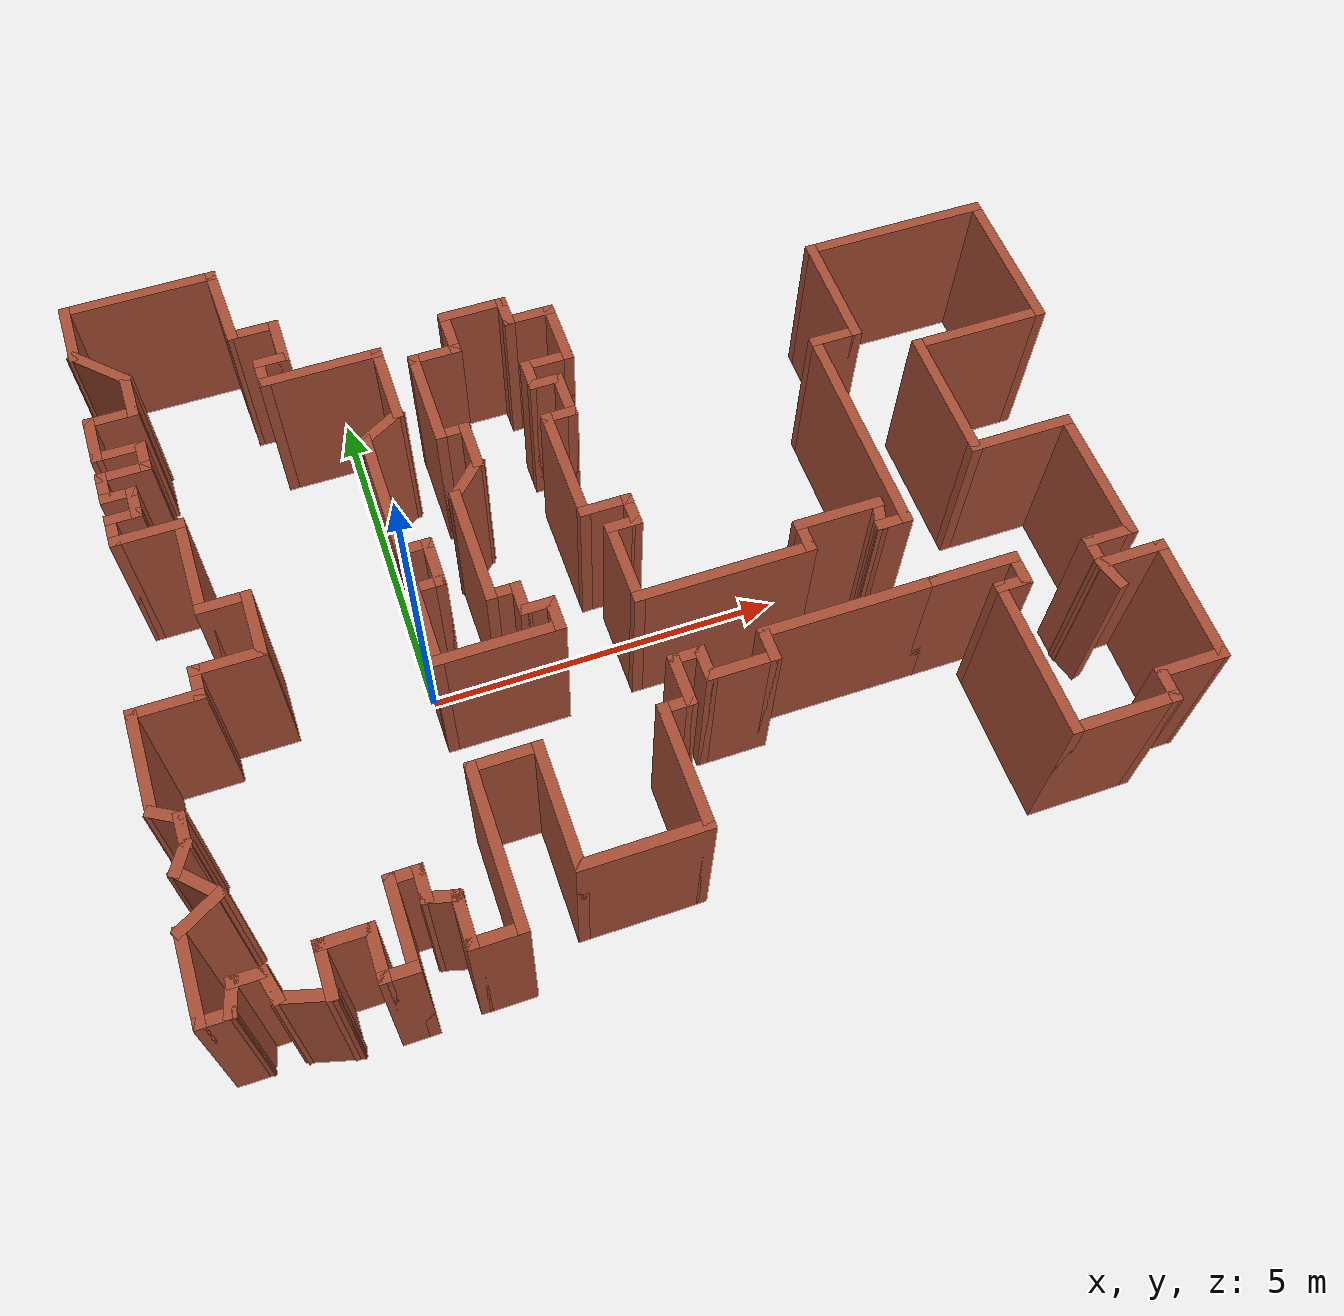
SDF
<?xml version='1.0'?>
<sdf version='1.6'>
  <model name='map_59'>
    <pose frame=''>2.96986 0.975899 0 0 -0 0</pose>
    <link name='Wall_0'>
      <collision name='Wall_0_Collision'>
        <geometry>
          <box>
            <size>2.25 0.15 2.5</size>
          </box>
        </geometry>
        <pose frame=''>0 0 1.25 0 -0 0</pose>
      </collision>
      <visual name='Wall_0_Visual'>
        <pose frame=''>0 0 1.25 0 -0 0</pose>
        <geometry>
          <box>
            <size>2.25 0.15 2.5</size>
          </box>
        </geometry>
        <material>
          <script>
            <uri>file://media/materials/scripts/gazebo.material</uri>
            <name>Gazebo/Bricks</name>
          </script>
          <ambient>1 1 1 1</ambient>
        </material>
        <meta>
          <layer>0</layer>
        </meta>
      </visual>
      <pose frame=''>-5.34713 5.38602 0 0 -0 3.14159</pose>
    </link>
    <link name='Wall_1'>
      <collision name='Wall_1_Collision'>
        <geometry>
          <box>
            <size>1 0.15 2.5</size>
          </box>
        </geometry>
        <pose frame=''>0 0 1.25 0 -0 0</pose>
      </collision>
      <visual name='Wall_1_Visual'>
        <pose frame=''>0 0 1.25 0 -0 0</pose>
        <geometry>
          <box>
            <size>1 0.15 2.5</size>
          </box>
        </geometry>
        <material>
          <script>
            <uri>file://media/materials/scripts/gazebo.material</uri>
            <name>Gazebo/Bricks</name>
          </script>
          <ambient>1 1 1 1</ambient>
        </material>
        <meta>
          <layer>0</layer>
        </meta>
      </visual>
      <pose frame=''>-6.39713 4.96102 0 0 -0 -1.5708</pose>
    </link>
    <link name='Wall_103'>
      <collision name='Wall_103_Collision'>
        <geometry>
          <box>
            <size>1 0.15 2.5</size>
          </box>
        </geometry>
        <pose frame=''>0 0 1.25 0 -0 0</pose>
      </collision>
      <visual name='Wall_103_Visual'>
        <pose frame=''>0 0 1.25 0 -0 0</pose>
        <geometry>
          <box>
            <size>1 0.15 2.5</size>
          </box>
        </geometry>
        <material>
          <script>
            <uri>file://media/materials/scripts/gazebo.material</uri>
            <name>Gazebo/Bricks</name>
          </script>
          <ambient>1 1 1 1</ambient>
        </material>
        <meta>
          <layer>0</layer>
        </meta>
      </visual>
      <pose frame=''>5.99854 -3.05386 0 0 -0 3.14159</pose>
    </link>
    <link name='Wall_104'>
      <collision name='Wall_104_Collision'>
        <geometry>
          <box>
            <size>0.5 0.15 2.5</size>
          </box>
        </geometry>
        <pose frame=''>0 0 1.25 0 -0 0</pose>
      </collision>
      <visual name='Wall_104_Visual'>
        <pose frame=''>0 0 1.25 0 -0 0</pose>
        <geometry>
          <box>
            <size>0.5 0.15 2.5</size>
          </box>
        </geometry>
        <material>
          <script>
            <uri>file://media/materials/scripts/gazebo.material</uri>
            <name>Gazebo/Bricks</name>
          </script>
          <ambient>1 1 1 1</ambient>
        </material>
        <meta>
          <layer>0</layer>
        </meta>
      </visual>
      <pose frame=''>5.57354 -2.87886 0 0 -0 1.5708</pose>
    </link>
    <link name='Wall_105'>
      <collision name='Wall_105_Collision'>
        <geometry>
          <box>
            <size>0.75 0.15 2.5</size>
          </box>
        </geometry>
        <pose frame=''>0 0 1.25 0 -0 0</pose>
      </collision>
      <visual name='Wall_105_Visual'>
        <pose frame=''>0 0 1.25 0 -0 0</pose>
        <geometry>
          <box>
            <size>0.75 0.15 2.5</size>
          </box>
        </geometry>
        <material>
          <script>
            <uri>file://media/materials/scripts/gazebo.material</uri>
            <name>Gazebo/Bricks</name>
          </script>
          <ambient>1 1 1 1</ambient>
        </material>
        <meta>
          <layer>0</layer>
        </meta>
      </visual>
      <pose frame=''>5.87354 -2.70386 0 0 -0 0</pose>
    </link>
    <link name='Wall_108'>
      <collision name='Wall_108_Collision'>
        <geometry>
          <box>
            <size>0.5 0.15 2.5</size>
          </box>
        </geometry>
        <pose frame=''>0 0 1.25 0 -0 0</pose>
      </collision>
      <visual name='Wall_108_Visual'>
        <pose frame=''>0 0 1.25 0 -0 0</pose>
        <geometry>
          <box>
            <size>0.5 0.15 2.5</size>
          </box>
        </geometry>
        <material>
          <script>
            <uri>file://media/materials/scripts/gazebo.material</uri>
            <name>Gazebo/Bricks</name>
          </script>
          <ambient>1 1 1 1</ambient>
        </material>
        <meta>
          <layer>0</layer>
        </meta>
      </visual>
      <pose frame=''>5.61884 -3.22289 0 0 -0 -1.309</pose>
    </link>
    <link name='Wall_114'>
      <collision name='Wall_114_Collision'>
        <geometry>
          <box>
            <size>1.5 0.15 2.5</size>
          </box>
        </geometry>
        <pose frame=''>0 0 1.25 0 -0 0</pose>
      </collision>
      <visual name='Wall_114_Visual'>
        <pose frame=''>0 0 1.25 0 -0 0</pose>
        <geometry>
          <box>
            <size>1.5 0.15 2.5</size>
          </box>
        </geometry>
        <material>
          <script>
            <uri>file://media/materials/scripts/gazebo.material</uri>
            <name>Gazebo/Bricks</name>
          </script>
          <ambient>1 1 1 1</ambient>
        </material>
        <meta>
          <layer>0</layer>
        </meta>
      </visual>
      <pose frame=''>4.86047 -5.06327 0 0 -0 0</pose>
    </link>
    <link name='Wall_115'>
      <collision name='Wall_115_Collision'>
        <geometry>
          <box>
            <size>0.5 0.15 2.5</size>
          </box>
        </geometry>
        <pose frame=''>0 0 1.25 0 -0 0</pose>
      </collision>
      <visual name='Wall_115_Visual'>
        <pose frame=''>0 0 1.25 0 -0 0</pose>
        <geometry>
          <box>
            <size>0.5 0.15 2.5</size>
          </box>
        </geometry>
        <material>
          <script>
            <uri>file://media/materials/scripts/gazebo.material</uri>
            <name>Gazebo/Bricks</name>
          </script>
          <ambient>1 1 1 1</ambient>
        </material>
        <meta>
          <layer>0</layer>
        </meta>
      </visual>
      <pose frame=''>5.53547 -4.88827 0 0 -0 1.5708</pose>
    </link>
    <link name='Wall_118'>
      <collision name='Wall_118_Collision'>
        <geometry>
          <box>
            <size>1 0.15 2.5</size>
          </box>
        </geometry>
        <pose frame=''>0 0 1.25 0 -0 0</pose>
      </collision>
      <visual name='Wall_118_Visual'>
        <pose frame=''>0 0 1.25 0 -0 0</pose>
        <geometry>
          <box>
            <size>1 0.15 2.5</size>
          </box>
        </geometry>
        <material>
          <script>
            <uri>file://media/materials/scripts/gazebo.material</uri>
            <name>Gazebo/Bricks</name>
          </script>
          <ambient>1 1 1 1</ambient>
        </material>
        <meta>
          <layer>0</layer>
        </meta>
      </visual>
      <pose frame=''>5.96047 -4.71327 0 0 -0 0</pose>
    </link>
    <link name='Wall_119'>
      <collision name='Wall_119_Collision'>
        <geometry>
          <box>
            <size>1.80985 0.15 2.5</size>
          </box>
        </geometry>
        <pose frame=''>0 0 1.25 0 -0 0</pose>
      </collision>
      <visual name='Wall_119_Visual'>
        <pose frame=''>0 0 1.25 0 -0 0</pose>
        <geometry>
          <box>
            <size>1.80985 0.15 2.5</size>
          </box>
        </geometry>
        <material>
          <script>
            <uri>file://media/materials/scripts/gazebo.material</uri>
            <name>Gazebo/Bricks</name>
          </script>
          <ambient>1 1 1 1</ambient>
        </material>
        <meta>
          <layer>0</layer>
        </meta>
      </visual>
      <pose frame=''>6.40451 -3.88356 0 0 -0 1.54786</pose>
    </link>
    <link name='Wall_121'>
      <collision name='Wall_121_Collision'>
        <geometry>
          <box>
            <size>2 0.15 2.5</size>
          </box>
        </geometry>
        <pose frame=''>0 0 1.25 0 -0 0</pose>
      </collision>
      <visual name='Wall_121_Visual'>
        <pose frame=''>0 0 1.25 0 -0 0</pose>
        <geometry>
          <box>
            <size>2 0.15 2.5</size>
          </box>
        </geometry>
        <material>
          <script>
            <uri>file://media/materials/scripts/gazebo.material</uri>
            <name>Gazebo/Bricks</name>
          </script>
          <ambient>1 1 1 1</ambient>
        </material>
        <meta>
          <layer>0</layer>
        </meta>
      </visual>
      <pose frame=''>4.82354 0.071143 0 0 -0 1.5708</pose>
    </link>
    <link name='Wall_122'>
      <collision name='Wall_122_Collision'>
        <geometry>
          <box>
            <size>2 0.15 2.5</size>
          </box>
        </geometry>
        <pose frame=''>0 0 1.25 0 -0 0</pose>
      </collision>
      <visual name='Wall_122_Visual'>
        <pose frame=''>0 0 1.25 0 -0 0</pose>
        <geometry>
          <box>
            <size>2 0.15 2.5</size>
          </box>
        </geometry>
        <material>
          <script>
            <uri>file://media/materials/scripts/gazebo.material</uri>
            <name>Gazebo/Bricks</name>
          </script>
          <ambient>1 1 1 1</ambient>
        </material>
        <meta>
          <layer>0</layer>
        </meta>
      </visual>
      <pose frame=''>5.74854 0.996143 0 0 -0 0</pose>
    </link>
    <link name='Wall_123'>
      <collision name='Wall_123_Collision'>
        <geometry>
          <box>
            <size>2.25 0.15 2.5</size>
          </box>
        </geometry>
        <pose frame=''>0 0 1.25 0 -0 0</pose>
      </collision>
      <visual name='Wall_123_Visual'>
        <pose frame=''>0 0 1.25 0 -0 0</pose>
        <geometry>
          <box>
            <size>2.25 0.15 2.5</size>
          </box>
        </geometry>
        <material>
          <script>
            <uri>file://media/materials/scripts/gazebo.material</uri>
            <name>Gazebo/Bricks</name>
          </script>
          <ambient>1 1 1 1</ambient>
        </material>
        <meta>
          <layer>0</layer>
        </meta>
      </visual>
      <pose frame=''>6.67354 2.04614 0 0 -0 1.5708</pose>
    </link>
    <link name='Wall_124'>
      <collision name='Wall_124_Collision'>
        <geometry>
          <box>
            <size>2.75 0.15 2.5</size>
          </box>
        </geometry>
        <pose frame=''>0 0 1.25 0 -0 0</pose>
      </collision>
      <visual name='Wall_124_Visual'>
        <pose frame=''>0 0 1.25 0 -0 0</pose>
        <geometry>
          <box>
            <size>2.75 0.15 2.5</size>
          </box>
        </geometry>
        <material>
          <script>
            <uri>file://media/materials/scripts/gazebo.material</uri>
            <name>Gazebo/Bricks</name>
          </script>
          <ambient>1 1 1 1</ambient>
        </material>
        <meta>
          <layer>0</layer>
        </meta>
      </visual>
      <pose frame=''>5.37354 3.09614 0 0 -0 3.14159</pose>
    </link>
    <link name='Wall_125'>
      <collision name='Wall_125_Collision'>
        <geometry>
          <box>
            <size>1.75 0.15 2.5</size>
          </box>
        </geometry>
        <pose frame=''>0 0 1.25 0 -0 0</pose>
      </collision>
      <visual name='Wall_125_Visual'>
        <pose frame=''>0 0 1.25 0 -0 0</pose>
        <geometry>
          <box>
            <size>1.75 0.15 2.5</size>
          </box>
        </geometry>
        <material>
          <script>
            <uri>file://media/materials/scripts/gazebo.material</uri>
            <name>Gazebo/Bricks</name>
          </script>
          <ambient>1 1 1 1</ambient>
        </material>
        <meta>
          <layer>0</layer>
        </meta>
      </visual>
      <pose frame=''>4.07354 2.29614 0 0 -0 -1.5708</pose>
    </link>
    <link name='Wall_126'>
      <collision name='Wall_126_Collision'>
        <geometry>
          <box>
            <size>0.75 0.15 2.5</size>
          </box>
        </geometry>
        <pose frame=''>0 0 1.25 0 -0 0</pose>
      </collision>
      <visual name='Wall_126_Visual'>
        <pose frame=''>0 0 1.25 0 -0 0</pose>
        <geometry>
          <box>
            <size>0.75 0.15 2.5</size>
          </box>
        </geometry>
        <material>
          <script>
            <uri>file://media/materials/scripts/gazebo.material</uri>
            <name>Gazebo/Bricks</name>
          </script>
          <ambient>1 1 1 1</ambient>
        </material>
        <meta>
          <layer>0</layer>
        </meta>
      </visual>
      <pose frame=''>3.77354 1.49614 0 0 -0 3.14159</pose>
    </link>
    <link name='Wall_127'>
      <collision name='Wall_127_Collision'>
        <geometry>
          <box>
            <size>3.25 0.15 2.5</size>
          </box>
        </geometry>
        <pose frame=''>0 0 1.25 0 -0 0</pose>
      </collision>
      <visual name='Wall_127_Visual'>
        <pose frame=''>0 0 1.25 0 -0 0</pose>
        <geometry>
          <box>
            <size>3.25 0.15 2.5</size>
          </box>
        </geometry>
        <material>
          <script>
            <uri>file://media/materials/scripts/gazebo.material</uri>
            <name>Gazebo/Bricks</name>
          </script>
          <ambient>1 1 1 1</ambient>
        </material>
        <meta>
          <layer>0</layer>
        </meta>
      </visual>
      <pose frame=''>3.47354 -0.053857 0 0 -0 -1.5708</pose>
    </link>
    <link name='Wall_128'>
      <collision name='Wall_128_Collision'>
        <geometry>
          <box>
            <size>0.5 0.15 2.5</size>
          </box>
        </geometry>
        <pose frame=''>0 0 1.25 0 -0 0</pose>
      </collision>
      <visual name='Wall_128_Visual'>
        <pose frame=''>0 0 1.25 0 -0 0</pose>
        <geometry>
          <box>
            <size>0.5 0.15 2.5</size>
          </box>
        </geometry>
        <material>
          <script>
            <uri>file://media/materials/scripts/gazebo.material</uri>
            <name>Gazebo/Bricks</name>
          </script>
          <ambient>1 1 1 1</ambient>
        </material>
        <meta>
          <layer>0</layer>
        </meta>
      </visual>
      <pose frame=''>3.29854 -1.60386 0 0 -0 3.14159</pose>
    </link>
    <link name='Wall_129'>
      <collision name='Wall_129_Collision'>
        <geometry>
          <box>
            <size>0.5 0.15 2.5</size>
          </box>
        </geometry>
        <pose frame=''>0 0 1.25 0 -0 0</pose>
      </collision>
      <visual name='Wall_129_Visual'>
        <pose frame=''>0 0 1.25 0 -0 0</pose>
        <geometry>
          <box>
            <size>0.5 0.15 2.5</size>
          </box>
        </geometry>
        <material>
          <script>
            <uri>file://media/materials/scripts/gazebo.material</uri>
            <name>Gazebo/Bricks</name>
          </script>
          <ambient>1 1 1 1</ambient>
        </material>
        <meta>
          <layer>0</layer>
        </meta>
      </visual>
      <pose frame=''>3.16884 -1.43482 0 0 -0 1.309</pose>
    </link>
    <link name='Wall_130'>
      <collision name='Wall_130_Collision'>
        <geometry>
          <box>
            <size>1.25 0.15 2.5</size>
          </box>
        </geometry>
        <pose frame=''>0 0 1.25 0 -0 0</pose>
      </collision>
      <visual name='Wall_130_Visual'>
        <pose frame=''>0 0 1.25 0 -0 0</pose>
        <geometry>
          <box>
            <size>1.25 0.15 2.5</size>
          </box>
        </geometry>
        <material>
          <script>
            <uri>file://media/materials/scripts/gazebo.material</uri>
            <name>Gazebo/Bricks</name>
          </script>
          <ambient>1 1 1 1</ambient>
        </material>
        <meta>
          <layer>0</layer>
        </meta>
      </visual>
      <pose frame=''>2.66413 -1.26578 0 0 -0 3.14159</pose>
    </link>
    <link name='Wall_131'>
      <collision name='Wall_131_Collision'>
        <geometry>
          <box>
            <size>0.5 0.15 2.5</size>
          </box>
        </geometry>
        <pose frame=''>0 0 1.25 0 -0 0</pose>
      </collision>
      <visual name='Wall_131_Visual'>
        <pose frame=''>0 0 1.25 0 -0 0</pose>
        <geometry>
          <box>
            <size>0.5 0.15 2.5</size>
          </box>
        </geometry>
        <material>
          <script>
            <uri>file://media/materials/scripts/gazebo.material</uri>
            <name>Gazebo/Bricks</name>
          </script>
          <ambient>1 1 1 1</ambient>
        </material>
        <meta>
          <layer>0</layer>
        </meta>
      </visual>
      <pose frame=''>2.11413 -1.44078 0 0 -0 -1.5708</pose>
    </link>
    <link name='Wall_132'>
      <collision name='Wall_132_Collision'>
        <geometry>
          <box>
            <size>2.5 0.15 2.5</size>
          </box>
        </geometry>
        <pose frame=''>0 0 1.25 0 -0 0</pose>
      </collision>
      <visual name='Wall_132_Visual'>
        <pose frame=''>0 0 1.25 0 -0 0</pose>
        <geometry>
          <box>
            <size>2.5 0.15 2.5</size>
          </box>
        </geometry>
        <material>
          <script>
            <uri>file://media/materials/scripts/gazebo.material</uri>
            <name>Gazebo/Bricks</name>
          </script>
          <ambient>1 1 1 1</ambient>
        </material>
        <meta>
          <layer>0</layer>
        </meta>
      </visual>
      <pose frame=''>0.93913 -1.61578 0 0 -0 3.14159</pose>
    </link>
    <link name='Wall_133'>
      <collision name='Wall_133_Collision'>
        <geometry>
          <box>
            <size>1.25 0.15 2.5</size>
          </box>
        </geometry>
        <pose frame=''>0 0 1.25 0 -0 0</pose>
      </collision>
      <visual name='Wall_133_Visual'>
        <pose frame=''>0 0 1.25 0 -0 0</pose>
        <geometry>
          <box>
            <size>1.25 0.15 2.5</size>
          </box>
        </geometry>
        <material>
          <script>
            <uri>file://media/materials/scripts/gazebo.material</uri>
            <name>Gazebo/Bricks</name>
          </script>
          <ambient>1 1 1 1</ambient>
        </material>
        <meta>
          <layer>0</layer>
        </meta>
      </visual>
      <pose frame=''>-0.23587 -1.06578 0 0 -0 1.5708</pose>
    </link>
    <link name='Wall_134'>
      <collision name='Wall_134_Collision'>
        <geometry>
          <box>
            <size>0.5 0.15 2.5</size>
          </box>
        </geometry>
        <pose frame=''>0 0 1.25 0 -0 0</pose>
      </collision>
      <visual name='Wall_134_Visual'>
        <pose frame=''>0 0 1.25 0 -0 0</pose>
        <geometry>
          <box>
            <size>0.5 0.15 2.5</size>
          </box>
        </geometry>
        <material>
          <script>
            <uri>file://media/materials/scripts/gazebo.material</uri>
            <name>Gazebo/Bricks</name>
          </script>
          <ambient>1 1 1 1</ambient>
        </material>
        <meta>
          <layer>0</layer>
        </meta>
      </visual>
      <pose frame=''>-0.06087 -0.515783 0 0 -0 0</pose>
    </link>
    <link name='Wall_135'>
      <collision name='Wall_135_Collision'>
        <geometry>
          <box>
            <size>0.5 0.15 2.5</size>
          </box>
        </geometry>
        <pose frame=''>0 0 1.25 0 -0 0</pose>
      </collision>
      <visual name='Wall_135_Visual'>
        <pose frame=''>0 0 1.25 0 -0 0</pose>
        <geometry>
          <box>
            <size>0.5 0.15 2.5</size>
          </box>
        </geometry>
        <material>
          <script>
            <uri>file://media/materials/scripts/gazebo.material</uri>
            <name>Gazebo/Bricks</name>
          </script>
          <ambient>1 1 1 1</ambient>
        </material>
        <meta>
          <layer>0</layer>
        </meta>
      </visual>
      <pose frame=''>0.11413 -0.340783 0 0 -0 1.5708</pose>
    </link>
    <link name='Wall_136'>
      <collision name='Wall_136_Collision'>
        <geometry>
          <box>
            <size>0.75 0.15 2.5</size>
          </box>
        </geometry>
        <pose frame=''>0 0 1.25 0 -0 0</pose>
      </collision>
      <visual name='Wall_136_Visual'>
        <pose frame=''>0 0 1.25 0 -0 0</pose>
        <geometry>
          <box>
            <size>0.75 0.15 2.5</size>
          </box>
        </geometry>
        <material>
          <script>
            <uri>file://media/materials/scripts/gazebo.material</uri>
            <name>Gazebo/Bricks</name>
          </script>
          <ambient>1 1 1 1</ambient>
        </material>
        <meta>
          <layer>0</layer>
        </meta>
      </visual>
      <pose frame=''>-0.18587 -0.165783 0 0 -0 3.14159</pose>
    </link>
    <link name='Wall_139'>
      <collision name='Wall_139_Collision'>
        <geometry>
          <box>
            <size>1.75 0.15 2.5</size>
          </box>
        </geometry>
        <pose frame=''>0 0 1.25 0 -0 0</pose>
      </collision>
      <visual name='Wall_139_Visual'>
        <pose frame=''>0 0 1.25 0 -0 0</pose>
        <geometry>
          <box>
            <size>1.75 0.15 2.5</size>
          </box>
        </geometry>
        <material>
          <script>
            <uri>file://media/materials/scripts/gazebo.material</uri>
            <name>Gazebo/Bricks</name>
          </script>
          <ambient>1 1 1 1</ambient>
        </material>
        <meta>
          <layer>0</layer>
        </meta>
      </visual>
      <pose frame=''>-0.48587 0.634217 0 0 -0 1.5708</pose>
    </link>
    <link name='Wall_140'>
      <collision name='Wall_140_Collision'>
        <geometry>
          <box>
            <size>0.5 0.15 2.5</size>
          </box>
        </geometry>
        <pose frame=''>0 0 1.25 0 -0 0</pose>
      </collision>
      <visual name='Wall_140_Visual'>
        <pose frame=''>0 0 1.25 0 -0 0</pose>
        <geometry>
          <box>
            <size>0.5 0.15 2.5</size>
          </box>
        </geometry>
        <material>
          <script>
            <uri>file://media/materials/scripts/gazebo.material</uri>
            <name>Gazebo/Bricks</name>
          </script>
          <ambient>1 1 1 1</ambient>
        </material>
        <meta>
          <layer>0</layer>
        </meta>
      </visual>
      <pose frame=''>-0.31087 1.43422 0 0 -0 0</pose>
    </link>
    <link name='Wall_143'>
      <collision name='Wall_143_Collision'>
        <geometry>
          <box>
            <size>0.75 0.15 2.5</size>
          </box>
        </geometry>
        <pose frame=''>0 0 1.25 0 -0 0</pose>
      </collision>
      <visual name='Wall_143_Visual'>
        <pose frame=''>0 0 1.25 0 -0 0</pose>
        <geometry>
          <box>
            <size>0.75 0.15 2.5</size>
          </box>
        </geometry>
        <material>
          <script>
            <uri>file://media/materials/scripts/gazebo.material</uri>
            <name>Gazebo/Bricks</name>
          </script>
          <ambient>1 1 1 1</ambient>
        </material>
        <meta>
          <layer>0</layer>
        </meta>
      </visual>
      <pose frame=''>-0.13587 1.73422 0 0 -0 1.5708</pose>
    </link>
    <link name='Wall_144'>
      <collision name='Wall_144_Collision'>
        <geometry>
          <box>
            <size>0.5 0.15 2.5</size>
          </box>
        </geometry>
        <pose frame=''>0 0 1.25 0 -0 0</pose>
      </collision>
      <visual name='Wall_144_Visual'>
        <pose frame=''>0 0 1.25 0 -0 0</pose>
        <geometry>
          <box>
            <size>0.5 0.15 2.5</size>
          </box>
        </geometry>
        <material>
          <script>
            <uri>file://media/materials/scripts/gazebo.material</uri>
            <name>Gazebo/Bricks</name>
          </script>
          <ambient>1 1 1 1</ambient>
        </material>
        <meta>
          <layer>0</layer>
        </meta>
      </visual>
      <pose frame=''>-0.31087 2.03422 0 0 -0 3.14159</pose>
    </link>
    <link name='Wall_145'>
      <collision name='Wall_145_Collision'>
        <geometry>
          <box>
            <size>0.5 0.15 2.5</size>
          </box>
        </geometry>
        <pose frame=''>0 0 1.25 0 -0 0</pose>
      </collision>
      <visual name='Wall_145_Visual'>
        <pose frame=''>0 0 1.25 0 -0 0</pose>
        <geometry>
          <box>
            <size>0.5 0.15 2.5</size>
          </box>
        </geometry>
        <material>
          <script>
            <uri>file://media/materials/scripts/gazebo.material</uri>
            <name>Gazebo/Bricks</name>
          </script>
          <ambient>1 1 1 1</ambient>
        </material>
        <meta>
          <layer>0</layer>
        </meta>
      </visual>
      <pose frame=''>-0.48587 2.20922 0 0 -0 1.5708</pose>
    </link>
    <link name='Wall_146'>
      <collision name='Wall_146_Collision'>
        <geometry>
          <box>
            <size>0.75 0.15 2.5</size>
          </box>
        </geometry>
        <pose frame=''>0 0 1.25 0 -0 0</pose>
      </collision>
      <visual name='Wall_146_Visual'>
        <pose frame=''>0 0 1.25 0 -0 0</pose>
        <geometry>
          <box>
            <size>0.75 0.15 2.5</size>
          </box>
        </geometry>
        <material>
          <script>
            <uri>file://media/materials/scripts/gazebo.material</uri>
            <name>Gazebo/Bricks</name>
          </script>
          <ambient>1 1 1 1</ambient>
        </material>
        <meta>
          <layer>0</layer>
        </meta>
      </visual>
      <pose frame=''>-0.18587 2.38422 0 0 -0 0</pose>
    </link>
    <link name='Wall_147'>
      <collision name='Wall_147_Collision'>
        <geometry>
          <box>
            <size>1 0.15 2.5</size>
          </box>
        </geometry>
        <pose frame=''>0 0 1.25 0 -0 0</pose>
      </collision>
      <visual name='Wall_147_Visual'>
        <pose frame=''>0 0 1.25 0 -0 0</pose>
        <geometry>
          <box>
            <size>1 0.15 2.5</size>
          </box>
        </geometry>
        <material>
          <script>
            <uri>file://media/materials/scripts/gazebo.material</uri>
            <name>Gazebo/Bricks</name>
          </script>
          <ambient>1 1 1 1</ambient>
        </material>
        <meta>
          <layer>0</layer>
        </meta>
      </visual>
      <pose frame=''>0.11413 2.80922 0 0 -0 1.5708</pose>
    </link>
    <link name='Wall_148'>
      <collision name='Wall_148_Collision'>
        <geometry>
          <box>
            <size>0.75 0.15 2.5</size>
          </box>
        </geometry>
        <pose frame=''>0 0 1.25 0 -0 0</pose>
      </collision>
      <visual name='Wall_148_Visual'>
        <pose frame=''>0 0 1.25 0 -0 0</pose>
        <geometry>
          <box>
            <size>0.75 0.15 2.5</size>
          </box>
        </geometry>
        <material>
          <script>
            <uri>file://media/materials/scripts/gazebo.material</uri>
            <name>Gazebo/Bricks</name>
          </script>
          <ambient>1 1 1 1</ambient>
        </material>
        <meta>
          <layer>0</layer>
        </meta>
      </visual>
      <pose frame=''>-0.18587 3.23422 0 0 -0 3.14159</pose>
    </link>
    <link name='Wall_149'>
      <collision name='Wall_149_Collision'>
        <geometry>
          <box>
            <size>0.5 0.15 2.5</size>
          </box>
        </geometry>
        <pose frame=''>0 0 1.25 0 -0 0</pose>
      </collision>
      <visual name='Wall_149_Visual'>
        <pose frame=''>0 0 1.25 0 -0 0</pose>
        <geometry>
          <box>
            <size>0.5 0.15 2.5</size>
          </box>
        </geometry>
        <material>
          <script>
            <uri>file://media/materials/scripts/gazebo.material</uri>
            <name>Gazebo/Bricks</name>
          </script>
          <ambient>1 1 1 1</ambient>
        </material>
        <meta>
          <layer>0</layer>
        </meta>
      </visual>
      <pose frame=''>-0.48587 3.40922 0 0 -0 1.5708</pose>
    </link>
    <link name='Wall_150'>
      <collision name='Wall_150_Collision'>
        <geometry>
          <box>
            <size>1 0.15 2.5</size>
          </box>
        </geometry>
        <pose frame=''>0 0 1.25 0 -0 0</pose>
      </collision>
      <visual name='Wall_150_Visual'>
        <pose frame=''>0 0 1.25 0 -0 0</pose>
        <geometry>
          <box>
            <size>1 0.15 2.5</size>
          </box>
        </geometry>
        <material>
          <script>
            <uri>file://media/materials/scripts/gazebo.material</uri>
            <name>Gazebo/Bricks</name>
          </script>
          <ambient>1 1 1 1</ambient>
        </material>
        <meta>
          <layer>0</layer>
        </meta>
      </visual>
      <pose frame=''>-0.91087 3.58422 0 0 -0 3.14159</pose>
    </link>
    <link name='Wall_151'>
      <collision name='Wall_151_Collision'>
        <geometry>
          <box>
            <size>0.75 0.15 2.5</size>
          </box>
        </geometry>
        <pose frame=''>0 0 1.25 0 -0 0</pose>
      </collision>
      <visual name='Wall_151_Visual'>
        <pose frame=''>0 0 1.25 0 -0 0</pose>
        <geometry>
          <box>
            <size>0.75 0.15 2.5</size>
          </box>
        </geometry>
        <material>
          <script>
            <uri>file://media/materials/scripts/gazebo.material</uri>
            <name>Gazebo/Bricks</name>
          </script>
          <ambient>1 1 1 1</ambient>
        </material>
        <meta>
          <layer>0</layer>
        </meta>
      </visual>
      <pose frame=''>-1.33587 3.28422 0 0 -0 -1.5708</pose>
    </link>
    <link name='Wall_152'>
      <collision name='Wall_152_Collision'>
        <geometry>
          <box>
            <size>0.75 0.15 2.5</size>
          </box>
        </geometry>
        <pose frame=''>0 0 1.25 0 -0 0</pose>
      </collision>
      <visual name='Wall_152_Visual'>
        <pose frame=''>0 0 1.25 0 -0 0</pose>
        <geometry>
          <box>
            <size>0.75 0.15 2.5</size>
          </box>
        </geometry>
        <material>
          <script>
            <uri>file://media/materials/scripts/gazebo.material</uri>
            <name>Gazebo/Bricks</name>
          </script>
          <ambient>1 1 1 1</ambient>
        </material>
        <meta>
          <layer>0</layer>
        </meta>
      </visual>
      <pose frame=''>-1.63587 2.98422 0 0 -0 3.14159</pose>
    </link>
    <link name='Wall_153'>
      <collision name='Wall_153_Collision'>
        <geometry>
          <box>
            <size>1.5 0.15 2.5</size>
          </box>
        </geometry>
        <pose frame=''>0 0 1.25 0 -0 0</pose>
      </collision>
      <visual name='Wall_153_Visual'>
        <pose frame=''>0 0 1.25 0 -0 0</pose>
        <geometry>
          <box>
            <size>1.5 0.15 2.5</size>
          </box>
        </geometry>
        <material>
          <script>
            <uri>file://media/materials/scripts/gazebo.material</uri>
            <name>Gazebo/Bricks</name>
          </script>
          <ambient>1 1 1 1</ambient>
        </material>
        <meta>
          <layer>0</layer>
        </meta>
      </visual>
      <pose frame=''>-1.93587 2.30922 0 0 -0 -1.5708</pose>
    </link>
    <link name='Wall_154'>
      <collision name='Wall_154_Collision'>
        <geometry>
          <box>
            <size>0.5 0.15 2.5</size>
          </box>
        </geometry>
        <pose frame=''>0 0 1.25 0 -0 0</pose>
      </collision>
      <visual name='Wall_154_Visual'>
        <pose frame=''>0 0 1.25 0 -0 0</pose>
        <geometry>
          <box>
            <size>0.5 0.15 2.5</size>
          </box>
        </geometry>
        <material>
          <script>
            <uri>file://media/materials/scripts/gazebo.material</uri>
            <name>Gazebo/Bricks</name>
          </script>
          <ambient>1 1 1 1</ambient>
        </material>
        <meta>
          <layer>0</layer>
        </meta>
      </visual>
      <pose frame=''>-1.76087 1.63422 0 0 -0 0</pose>
    </link>
    <link name='Wall_155'>
      <collision name='Wall_155_Collision'>
        <geometry>
          <box>
            <size>0.75 0.15 2.5</size>
          </box>
        </geometry>
        <pose frame=''>0 0 1.25 0 -0 0</pose>
      </collision>
      <visual name='Wall_155_Visual'>
        <pose frame=''>0 0 1.25 0 -0 0</pose>
        <geometry>
          <box>
            <size>0.75 0.15 2.5</size>
          </box>
        </geometry>
        <material>
          <script>
            <uri>file://media/materials/scripts/gazebo.material</uri>
            <name>Gazebo/Bricks</name>
          </script>
          <ambient>1 1 1 1</ambient>
        </material>
        <meta>
          <layer>0</layer>
        </meta>
      </visual>
      <pose frame=''>-1.58587 1.33422 0 0 -0 -1.5708</pose>
    </link>
    <link name='Wall_156'>
      <collision name='Wall_156_Collision'>
        <geometry>
          <box>
            <size>0.75 0.15 2.5</size>
          </box>
        </geometry>
        <pose frame=''>0 0 1.25 0 -0 0</pose>
      </collision>
      <visual name='Wall_156_Visual'>
        <pose frame=''>0 0 1.25 0 -0 0</pose>
        <geometry>
          <box>
            <size>0.75 0.15 2.5</size>
          </box>
        </geometry>
        <material>
          <script>
            <uri>file://media/materials/scripts/gazebo.material</uri>
            <name>Gazebo/Bricks</name>
          </script>
          <ambient>1 1 1 1</ambient>
        </material>
        <meta>
          <layer>0</layer>
        </meta>
      </visual>
      <pose frame=''>-1.798 0.822085 0 0 -0 -2.35619</pose>
    </link>
    <link name='Wall_160'>
      <collision name='Wall_160_Collision'>
        <geometry>
          <box>
            <size>1.75 0.15 2.5</size>
          </box>
        </geometry>
        <pose frame=''>0 0 1.25 0 -0 0</pose>
      </collision>
      <visual name='Wall_160_Visual'>
        <pose frame=''>0 0 1.25 0 -0 0</pose>
        <geometry>
          <box>
            <size>1.75 0.15 2.5</size>
          </box>
        </geometry>
        <material>
          <script>
            <uri>file://media/materials/scripts/gazebo.material</uri>
            <name>Gazebo/Bricks</name>
          </script>
          <ambient>1 1 1 1</ambient>
        </material>
        <meta>
          <layer>0</layer>
        </meta>
      </visual>
      <pose frame=''>-2.01013 -0.190047 0 0 -0 -1.5708</pose>
    </link>
    <link name='Wall_161'>
      <collision name='Wall_161_Collision'>
        <geometry>
          <box>
            <size>0.5 0.15 2.5</size>
          </box>
        </geometry>
        <pose frame=''>0 0 1.25 0 -0 0</pose>
      </collision>
      <visual name='Wall_161_Visual'>
        <pose frame=''>0 0 1.25 0 -0 0</pose>
        <geometry>
          <box>
            <size>0.5 0.15 2.5</size>
          </box>
        </geometry>
        <material>
          <script>
            <uri>file://media/materials/scripts/gazebo.material</uri>
            <name>Gazebo/Bricks</name>
          </script>
          <ambient>1 1 1 1</ambient>
        </material>
        <meta>
          <layer>0</layer>
        </meta>
      </visual>
      <pose frame=''>-1.83513 -0.990047 0 0 -0 0</pose>
    </link>
    <link name='Wall_162'>
      <collision name='Wall_162_Collision'>
        <geometry>
          <box>
            <size>0.5 0.15 2.5</size>
          </box>
        </geometry>
        <pose frame=''>0 0 1.25 0 -0 0</pose>
      </collision>
      <visual name='Wall_162_Visual'>
        <pose frame=''>0 0 1.25 0 -0 0</pose>
        <geometry>
          <box>
            <size>0.5 0.15 2.5</size>
          </box>
        </geometry>
        <material>
          <script>
            <uri>file://media/materials/scripts/gazebo.material</uri>
            <name>Gazebo/Bricks</name>
          </script>
          <ambient>1 1 1 1</ambient>
        </material>
        <meta>
          <layer>0</layer>
        </meta>
      </visual>
      <pose frame=''>-1.66013 -1.16505 0 0 -0 -1.5708</pose>
    </link>
    <link name='Wall_163'>
      <collision name='Wall_163_Collision'>
        <geometry>
          <box>
            <size>0.5 0.15 2.5</size>
          </box>
        </geometry>
        <pose frame=''>0 0 1.25 0 -0 0</pose>
      </collision>
      <visual name='Wall_163_Visual'>
        <pose frame=''>0 0 1.25 0 -0 0</pose>
        <geometry>
          <box>
            <size>0.5 0.15 2.5</size>
          </box>
        </geometry>
        <material>
          <script>
            <uri>file://media/materials/scripts/gazebo.material</uri>
            <name>Gazebo/Bricks</name>
          </script>
          <ambient>1 1 1 1</ambient>
        </material>
        <meta>
          <layer>0</layer>
        </meta>
      </visual>
      <pose frame=''>-1.48513 -1.34005 0 0 -0 0</pose>
    </link>
    <link name='Wall_164'>
      <collision name='Wall_164_Collision'>
        <geometry>
          <box>
            <size>0.5 0.15 2.5</size>
          </box>
        </geometry>
        <pose frame=''>0 0 1.25 0 -0 0</pose>
      </collision>
      <visual name='Wall_164_Visual'>
        <pose frame=''>0 0 1.25 0 -0 0</pose>
        <geometry>
          <box>
            <size>0.5 0.15 2.5</size>
          </box>
        </geometry>
        <material>
          <script>
            <uri>file://media/materials/scripts/gazebo.material</uri>
            <name>Gazebo/Bricks</name>
          </script>
          <ambient>1 1 1 1</ambient>
        </material>
        <meta>
          <layer>0</layer>
        </meta>
      </visual>
      <pose frame=''>-1.31013 -1.51505 0 0 -0 -1.5708</pose>
    </link>
    <link name='Wall_165'>
      <collision name='Wall_165_Collision'>
        <geometry>
          <box>
            <size>1.75 0.15 2.5</size>
          </box>
        </geometry>
        <pose frame=''>0 0 1.25 0 -0 0</pose>
      </collision>
      <visual name='Wall_165_Visual'>
        <pose frame=''>0 0 1.25 0 -0 0</pose>
        <geometry>
          <box>
            <size>1.75 0.15 2.5</size>
          </box>
        </geometry>
        <material>
          <script>
            <uri>file://media/materials/scripts/gazebo.material</uri>
            <name>Gazebo/Bricks</name>
          </script>
          <ambient>1 1 1 1</ambient>
        </material>
        <meta>
          <layer>0</layer>
        </meta>
      </visual>
      <pose frame=''>-2.11013 -1.69005 0 0 -0 3.14159</pose>
    </link>
    <link name='Wall_166'>
      <collision name='Wall_166_Collision'>
        <geometry>
          <box>
            <size>1.25 0.15 2.5</size>
          </box>
        </geometry>
        <pose frame=''>0 0 1.25 0 -0 0</pose>
      </collision>
      <visual name='Wall_166_Visual'>
        <pose frame=''>0 0 1.25 0 -0 0</pose>
        <geometry>
          <box>
            <size>1.25 0.15 2.5</size>
          </box>
        </geometry>
        <material>
          <script>
            <uri>file://media/materials/scripts/gazebo.material</uri>
            <name>Gazebo/Bricks</name>
          </script>
          <ambient>1 1 1 1</ambient>
        </material>
        <meta>
          <layer>0</layer>
        </meta>
      </visual>
      <pose frame=''>-2.91013 -1.14005 0 0 -0 1.5708</pose>
    </link>
    <link name='Wall_167'>
      <collision name='Wall_167_Collision'>
        <geometry>
          <box>
            <size>0.5 0.15 2.5</size>
          </box>
        </geometry>
        <pose frame=''>0 0 1.25 0 -0 0</pose>
      </collision>
      <visual name='Wall_167_Visual'>
        <pose frame=''>0 0 1.25 0 -0 0</pose>
        <geometry>
          <box>
            <size>0.5 0.15 2.5</size>
          </box>
        </geometry>
        <material>
          <script>
            <uri>file://media/materials/scripts/gazebo.material</uri>
            <name>Gazebo/Bricks</name>
          </script>
          <ambient>1 1 1 1</ambient>
        </material>
        <meta>
          <layer>0</layer>
        </meta>
      </visual>
      <pose frame=''>-2.73513 -0.590047 0 0 -0 0</pose>
    </link>
    <link name='Wall_168'>
      <collision name='Wall_168_Collision'>
        <geometry>
          <box>
            <size>0.75 0.15 2.5</size>
          </box>
        </geometry>
        <pose frame=''>0 0 1.25 0 -0 0</pose>
      </collision>
      <visual name='Wall_168_Visual'>
        <pose frame=''>0 0 1.25 0 -0 0</pose>
        <geometry>
          <box>
            <size>0.75 0.15 2.5</size>
          </box>
        </geometry>
        <material>
          <script>
            <uri>file://media/materials/scripts/gazebo.material</uri>
            <name>Gazebo/Bricks</name>
          </script>
          <ambient>1 1 1 1</ambient>
        </material>
        <meta>
          <layer>0</layer>
        </meta>
      </visual>
      <pose frame=''>-2.56013 -0.290047 0 0 -0 1.5708</pose>
    </link>
    <link name='Wall_169'>
      <collision name='Wall_169_Collision'>
        <geometry>
          <box>
            <size>0.5 0.15 2.5</size>
          </box>
        </geometry>
        <pose frame=''>0 0 1.25 0 -0 0</pose>
      </collision>
      <visual name='Wall_169_Visual'>
        <pose frame=''>0 0 1.25 0 -0 0</pose>
        <geometry>
          <box>
            <size>0.5 0.15 2.5</size>
          </box>
        </geometry>
        <material>
          <script>
            <uri>file://media/materials/scripts/gazebo.material</uri>
            <name>Gazebo/Bricks</name>
          </script>
          <ambient>1 1 1 1</ambient>
        </material>
        <meta>
          <layer>0</layer>
        </meta>
      </visual>
      <pose frame=''>-2.73513 0.009953 0 0 -0 3.14159</pose>
    </link>
    <link name='Wall_17'>
      <collision name='Wall_17_Collision'>
        <geometry>
          <box>
            <size>0.5 0.15 2.5</size>
          </box>
        </geometry>
        <pose frame=''>0 0 1.25 0 -0 0</pose>
      </collision>
      <visual name='Wall_17_Visual'>
        <pose frame=''>0 0 1.25 0 -0 0</pose>
        <geometry>
          <box>
            <size>0.5 0.15 2.5</size>
          </box>
        </geometry>
        <material>
          <script>
            <uri>file://media/materials/scripts/gazebo.material</uri>
            <name>Gazebo/Bricks</name>
          </script>
          <ambient>1 1 1 1</ambient>
        </material>
        <meta>
          <layer>0</layer>
        </meta>
      </visual>
      <pose frame=''>-6.39609 2.20998 0 0 -0 -1.5708</pose>
    </link>
    <link name='Wall_170'>
      <collision name='Wall_170_Collision'>
        <geometry>
          <box>
            <size>2 0.15 2.5</size>
          </box>
        </geometry>
        <pose frame=''>0 0 1.25 0 -0 0</pose>
      </collision>
      <visual name='Wall_170_Visual'>
        <pose frame=''>0 0 1.25 0 -0 0</pose>
        <geometry>
          <box>
            <size>2 0.15 2.5</size>
          </box>
        </geometry>
        <material>
          <script>
            <uri>file://media/materials/scripts/gazebo.material</uri>
            <name>Gazebo/Bricks</name>
          </script>
          <ambient>1 1 1 1</ambient>
        </material>
        <meta>
          <layer>0</layer>
        </meta>
      </visual>
      <pose frame=''>-2.91013 0.934953 0 0 -0 1.5708</pose>
    </link>
    <link name='Wall_171'>
      <collision name='Wall_171_Collision'>
        <geometry>
          <box>
            <size>0.75 0.15 2.5</size>
          </box>
        </geometry>
        <pose frame=''>0 0 1.25 0 -0 0</pose>
      </collision>
      <visual name='Wall_171_Visual'>
        <pose frame=''>0 0 1.25 0 -0 0</pose>
        <geometry>
          <box>
            <size>0.75 0.15 2.5</size>
          </box>
        </geometry>
        <material>
          <script>
            <uri>file://media/materials/scripts/gazebo.material</uri>
            <name>Gazebo/Bricks</name>
          </script>
          <ambient>1 1 1 1</ambient>
        </material>
        <meta>
          <layer>0</layer>
        </meta>
      </visual>
      <pose frame=''>-2.65033 2.00995 0 0 -0 0.523599</pose>
    </link>
    <link name='Wall_172'>
      <collision name='Wall_172_Collision'>
        <geometry>
          <box>
            <size>1.25 0.15 2.5</size>
          </box>
        </geometry>
        <pose frame=''>0 0 1.25 0 -0 0</pose>
      </collision>
      <visual name='Wall_172_Visual'>
        <pose frame=''>0 0 1.25 0 -0 0</pose>
        <geometry>
          <box>
            <size>1.25 0.15 2.5</size>
          </box>
        </geometry>
        <material>
          <script>
            <uri>file://media/materials/scripts/gazebo.material</uri>
            <name>Gazebo/Bricks</name>
          </script>
          <ambient>1 1 1 1</ambient>
        </material>
        <meta>
          <layer>0</layer>
        </meta>
      </visual>
      <pose frame=''>-2.39052 2.70995 0 0 -0 1.5708</pose>
    </link>
    <link name='Wall_173'>
      <collision name='Wall_173_Collision'>
        <geometry>
          <box>
            <size>1.75 0.15 2.5</size>
          </box>
        </geometry>
        <pose frame=''>0 0 1.25 0 -0 0</pose>
      </collision>
      <visual name='Wall_173_Visual'>
        <pose frame=''>0 0 1.25 0 -0 0</pose>
        <geometry>
          <box>
            <size>1.75 0.15 2.5</size>
          </box>
        </geometry>
        <material>
          <script>
            <uri>file://media/materials/scripts/gazebo.material</uri>
            <name>Gazebo/Bricks</name>
          </script>
          <ambient>1 1 1 1</ambient>
        </material>
        <meta>
          <layer>0</layer>
        </meta>
      </visual>
      <pose frame=''>-3.19052 3.25995 0 0 -0 3.14159</pose>
    </link>
    <link name='Wall_174'>
      <collision name='Wall_174_Collision'>
        <geometry>
          <box>
            <size>0.5 0.15 2.5</size>
          </box>
        </geometry>
        <pose frame=''>0 0 1.25 0 -0 0</pose>
      </collision>
      <visual name='Wall_174_Visual'>
        <pose frame=''>0 0 1.25 0 -0 0</pose>
        <geometry>
          <box>
            <size>0.5 0.15 2.5</size>
          </box>
        </geometry>
        <material>
          <script>
            <uri>file://media/materials/scripts/gazebo.material</uri>
            <name>Gazebo/Bricks</name>
          </script>
          <ambient>1 1 1 1</ambient>
        </material>
        <meta>
          <layer>0</layer>
        </meta>
      </visual>
      <pose frame=''>-3.99052 3.43495 0 0 -0 1.5708</pose>
    </link>
    <link name='Wall_175'>
      <collision name='Wall_175_Collision'>
        <geometry>
          <box>
            <size>0.5 0.15 2.5</size>
          </box>
        </geometry>
        <pose frame=''>0 0 1.25 0 -0 0</pose>
      </collision>
      <visual name='Wall_175_Visual'>
        <pose frame=''>0 0 1.25 0 -0 0</pose>
        <geometry>
          <box>
            <size>0.5 0.15 2.5</size>
          </box>
        </geometry>
        <material>
          <script>
            <uri>file://media/materials/scripts/gazebo.material</uri>
            <name>Gazebo/Bricks</name>
          </script>
          <ambient>1 1 1 1</ambient>
        </material>
        <meta>
          <layer>0</layer>
        </meta>
      </visual>
      <pose frame=''>-3.81552 3.60995 0 0 -0 0</pose>
    </link>
    <link name='Wall_176'>
      <collision name='Wall_176_Collision'>
        <geometry>
          <box>
            <size>0.75 0.15 2.5</size>
          </box>
        </geometry>
        <pose frame=''>0 0 1.25 0 -0 0</pose>
      </collision>
      <visual name='Wall_176_Visual'>
        <pose frame=''>0 0 1.25 0 -0 0</pose>
        <geometry>
          <box>
            <size>0.75 0.15 2.5</size>
          </box>
        </geometry>
        <material>
          <script>
            <uri>file://media/materials/scripts/gazebo.material</uri>
            <name>Gazebo/Bricks</name>
          </script>
          <ambient>1 1 1 1</ambient>
        </material>
        <meta>
          <layer>0</layer>
        </meta>
      </visual>
      <pose frame=''>-3.64052 3.90995 0 0 -0 1.5708</pose>
    </link>
    <link name='Wall_177'>
      <collision name='Wall_177_Collision'>
        <geometry>
          <box>
            <size>0.75 0.15 2.5</size>
          </box>
        </geometry>
        <pose frame=''>0 0 1.25 0 -0 0</pose>
      </collision>
      <visual name='Wall_177_Visual'>
        <pose frame=''>0 0 1.25 0 -0 0</pose>
        <geometry>
          <box>
            <size>0.75 0.15 2.5</size>
          </box>
        </geometry>
        <material>
          <script>
            <uri>file://media/materials/scripts/gazebo.material</uri>
            <name>Gazebo/Bricks</name>
          </script>
          <ambient>1 1 1 1</ambient>
        </material>
        <meta>
          <layer>0</layer>
        </meta>
      </visual>
      <pose frame=''>-3.94052 4.20995 0 0 -0 3.14159</pose>
    </link>
    <link name='Wall_178'>
      <collision name='Wall_178_Collision'>
        <geometry>
          <box>
            <size>1.32743 0.15 2.5</size>
          </box>
        </geometry>
        <pose frame=''>0 0 1.25 0 -0 0</pose>
      </collision>
      <visual name='Wall_178_Visual'>
        <pose frame=''>0 0 1.25 0 -0 0</pose>
        <geometry>
          <box>
            <size>1.32743 0.15 2.5</size>
          </box>
        </geometry>
        <material>
          <script>
            <uri>file://media/materials/scripts/gazebo.material</uri>
            <name>Gazebo/Bricks</name>
          </script>
          <ambient>1 1 1 1</ambient>
        </material>
        <meta>
          <layer>0</layer>
        </meta>
      </visual>
      <pose frame=''>-4.26883 4.79799 0 0 -0 1.6189</pose>
    </link>
    <link name='Wall_18'>
      <collision name='Wall_18_Collision'>
        <geometry>
          <box>
            <size>0.5 0.15 2.5</size>
          </box>
        </geometry>
        <pose frame=''>0 0 1.25 0 -0 0</pose>
      </collision>
      <visual name='Wall_18_Visual'>
        <pose frame=''>0 0 1.25 0 -0 0</pose>
        <geometry>
          <box>
            <size>0.5 0.15 2.5</size>
          </box>
        </geometry>
        <material>
          <script>
            <uri>file://media/materials/scripts/gazebo.material</uri>
            <name>Gazebo/Bricks</name>
          </script>
          <ambient>1 1 1 1</ambient>
        </material>
        <meta>
          <layer>0</layer>
        </meta>
      </visual>
      <pose frame=''>-6.22109 2.03498 0 0 -0 0</pose>
    </link>
    <link name='Wall_19'>
      <collision name='Wall_19_Collision'>
        <geometry>
          <box>
            <size>0.5 0.15 2.5</size>
          </box>
        </geometry>
        <pose frame=''>0 0 1.25 0 -0 0</pose>
      </collision>
      <visual name='Wall_19_Visual'>
        <pose frame=''>0 0 1.25 0 -0 0</pose>
        <geometry>
          <box>
            <size>0.5 0.15 2.5</size>
          </box>
        </geometry>
        <material>
          <script>
            <uri>file://media/materials/scripts/gazebo.material</uri>
            <name>Gazebo/Bricks</name>
          </script>
          <ambient>1 1 1 1</ambient>
        </material>
        <meta>
          <layer>0</layer>
        </meta>
      </visual>
      <pose frame=''>-6.04609 1.85998 0 0 -0 -1.5708</pose>
    </link>
    <link name='Wall_2'>
      <collision name='Wall_2_Collision'>
        <geometry>
          <box>
            <size>1 0.15 2.5</size>
          </box>
        </geometry>
        <pose frame=''>0 0 1.25 0 -0 0</pose>
      </collision>
      <visual name='Wall_2_Visual'>
        <pose frame=''>0 0 1.25 0 -0 0</pose>
        <geometry>
          <box>
            <size>1 0.15 2.5</size>
          </box>
        </geometry>
        <material>
          <script>
            <uri>file://media/materials/scripts/gazebo.material</uri>
            <name>Gazebo/Bricks</name>
          </script>
          <ambient>1 1 1 1</ambient>
        </material>
        <meta>
          <layer>0</layer>
        </meta>
      </visual>
      <pose frame=''>-6.09661 4.2355 0 0 -0 -0.785398</pose>
    </link>
    <link name='Wall_20'>
      <collision name='Wall_20_Collision'>
        <geometry>
          <box>
            <size>0.5 0.15 2.5</size>
          </box>
        </geometry>
        <pose frame=''>0 0 1.25 0 -0 0</pose>
      </collision>
      <visual name='Wall_20_Visual'>
        <pose frame=''>0 0 1.25 0 -0 0</pose>
        <geometry>
          <box>
            <size>0.5 0.15 2.5</size>
          </box>
        </geometry>
        <material>
          <script>
            <uri>file://media/materials/scripts/gazebo.material</uri>
            <name>Gazebo/Bricks</name>
          </script>
          <ambient>1 1 1 1</ambient>
        </material>
        <meta>
          <layer>0</layer>
        </meta>
      </visual>
      <pose frame=''>-6.22109 1.68498 0 0 -0 3.14159</pose>
    </link>
    <link name='Wall_21'>
      <collision name='Wall_21_Collision'>
        <geometry>
          <box>
            <size>0.5 0.15 2.5</size>
          </box>
        </geometry>
        <pose frame=''>0 0 1.25 0 -0 0</pose>
      </collision>
      <visual name='Wall_21_Visual'>
        <pose frame=''>0 0 1.25 0 -0 0</pose>
        <geometry>
          <box>
            <size>0.5 0.15 2.5</size>
          </box>
        </geometry>
        <material>
          <script>
            <uri>file://media/materials/scripts/gazebo.material</uri>
            <name>Gazebo/Bricks</name>
          </script>
          <ambient>1 1 1 1</ambient>
        </material>
        <meta>
          <layer>0</layer>
        </meta>
      </visual>
      <pose frame=''>-6.39609 1.50998 0 0 -0 -1.5708</pose>
    </link>
    <link name='Wall_24'>
      <collision name='Wall_24_Collision'>
        <geometry>
          <box>
            <size>1 0.15 2.5</size>
          </box>
        </geometry>
        <pose frame=''>0 0 1.25 0 -0 0</pose>
      </collision>
      <visual name='Wall_24_Visual'>
        <pose frame=''>0 0 1.25 0 -0 0</pose>
        <geometry>
          <box>
            <size>1 0.15 2.5</size>
          </box>
        </geometry>
        <material>
          <script>
            <uri>file://media/materials/scripts/gazebo.material</uri>
            <name>Gazebo/Bricks</name>
          </script>
          <ambient>1 1 1 1</ambient>
        </material>
        <meta>
          <layer>0</layer>
        </meta>
      </visual>
      <pose frame=''>-5.97109 1.33498 0 0 -0 0</pose>
    </link>
    <link name='Wall_25'>
      <collision name='Wall_25_Collision'>
        <geometry>
          <box>
            <size>1.5 0.15 2.5</size>
          </box>
        </geometry>
        <pose frame=''>0 0 1.25 0 -0 0</pose>
      </collision>
      <visual name='Wall_25_Visual'>
        <pose frame=''>0 0 1.25 0 -0 0</pose>
        <geometry>
          <box>
            <size>1.5 0.15 2.5</size>
          </box>
        </geometry>
        <material>
          <script>
            <uri>file://media/materials/scripts/gazebo.material</uri>
            <name>Gazebo/Bricks</name>
          </script>
          <ambient>1 1 1 1</ambient>
        </material>
        <meta>
          <layer>0</layer>
        </meta>
      </visual>
      <pose frame=''>-5.54609 0.65998 0 0 -0 -1.5708</pose>
    </link>
    <link name='Wall_26'>
      <collision name='Wall_26_Collision'>
        <geometry>
          <box>
            <size>0.75 0.15 2.5</size>
          </box>
        </geometry>
        <pose frame=''>0 0 1.25 0 -0 0</pose>
      </collision>
      <visual name='Wall_26_Visual'>
        <pose frame=''>0 0 1.25 0 -0 0</pose>
        <geometry>
          <box>
            <size>0.75 0.15 2.5</size>
          </box>
        </geometry>
        <material>
          <script>
            <uri>file://media/materials/scripts/gazebo.material</uri>
            <name>Gazebo/Bricks</name>
          </script>
          <ambient>1 1 1 1</ambient>
        </material>
        <meta>
          <layer>0</layer>
        </meta>
      </visual>
      <pose frame=''>-5.24609 -0.01502 0 0 -0 0</pose>
    </link>
    <link name='Wall_27'>
      <collision name='Wall_27_Collision'>
        <geometry>
          <box>
            <size>1 0.15 2.5</size>
          </box>
        </geometry>
        <pose frame=''>0 0 1.25 0 -0 0</pose>
      </collision>
      <visual name='Wall_27_Visual'>
        <pose frame=''>0 0 1.25 0 -0 0</pose>
        <geometry>
          <box>
            <size>1 0.15 2.5</size>
          </box>
        </geometry>
        <material>
          <script>
            <uri>file://media/materials/scripts/gazebo.material</uri>
            <name>Gazebo/Bricks</name>
          </script>
          <ambient>1 1 1 1</ambient>
        </material>
        <meta>
          <layer>0</layer>
        </meta>
      </visual>
      <pose frame=''>-4.94609 -0.44002 0 0 -0 -1.5708</pose>
    </link>
    <link name='Wall_28'>
      <collision name='Wall_28_Collision'>
        <geometry>
          <box>
            <size>1 0.15 2.5</size>
          </box>
        </geometry>
        <pose frame=''>0 0 1.25 0 -0 0</pose>
      </collision>
      <visual name='Wall_28_Visual'>
        <pose frame=''>0 0 1.25 0 -0 0</pose>
        <geometry>
          <box>
            <size>1 0.15 2.5</size>
          </box>
        </geometry>
        <material>
          <script>
            <uri>file://media/materials/scripts/gazebo.material</uri>
            <name>Gazebo/Bricks</name>
          </script>
          <ambient>1 1 1 1</ambient>
        </material>
        <meta>
          <layer>0</layer>
        </meta>
      </visual>
      <pose frame=''>-5.37109 -0.86502 0 0 -0 3.14159</pose>
    </link>
    <link name='Wall_29'>
      <collision name='Wall_29_Collision'>
        <geometry>
          <box>
            <size>0.5 0.15 2.5</size>
          </box>
        </geometry>
        <pose frame=''>0 0 1.25 0 -0 0</pose>
      </collision>
      <visual name='Wall_29_Visual'>
        <pose frame=''>0 0 1.25 0 -0 0</pose>
        <geometry>
          <box>
            <size>0.5 0.15 2.5</size>
          </box>
        </geometry>
        <material>
          <script>
            <uri>file://media/materials/scripts/gazebo.material</uri>
            <name>Gazebo/Bricks</name>
          </script>
          <ambient>1 1 1 1</ambient>
        </material>
        <meta>
          <layer>0</layer>
        </meta>
      </visual>
      <pose frame=''>-5.79609 -1.04002 0 0 -0 -1.5708</pose>
    </link>
    <link name='Wall_3'>
      <collision name='Wall_3_Collision'>
        <geometry>
          <box>
            <size>0.75 0.15 2.5</size>
          </box>
        </geometry>
        <pose frame=''>0 0 1.25 0 -0 0</pose>
      </collision>
      <visual name='Wall_3_Visual'>
        <pose frame=''>0 0 1.25 0 -0 0</pose>
        <geometry>
          <box>
            <size>0.75 0.15 2.5</size>
          </box>
        </geometry>
        <material>
          <script>
            <uri>file://media/materials/scripts/gazebo.material</uri>
            <name>Gazebo/Bricks</name>
          </script>
          <ambient>1 1 1 1</ambient>
        </material>
        <meta>
          <layer>0</layer>
        </meta>
      </visual>
      <pose frame=''>-5.79609 3.63498 0 0 -0 -1.5708</pose>
    </link>
    <link name='Wall_32'>
      <collision name='Wall_32_Collision'>
        <geometry>
          <box>
            <size>1 0.15 2.5</size>
          </box>
        </geometry>
        <pose frame=''>0 0 1.25 0 -0 0</pose>
      </collision>
      <visual name='Wall_32_Visual'>
        <pose frame=''>0 0 1.25 0 -0 0</pose>
        <geometry>
          <box>
            <size>1 0.15 2.5</size>
          </box>
        </geometry>
        <material>
          <script>
            <uri>file://media/materials/scripts/gazebo.material</uri>
            <name>Gazebo/Bricks</name>
          </script>
          <ambient>1 1 1 1</ambient>
        </material>
        <meta>
          <layer>0</layer>
        </meta>
      </visual>
      <pose frame=''>-6.22109 -1.21502 0 0 -0 3.14159</pose>
    </link>
    <link name='Wall_33'>
      <collision name='Wall_33_Collision'>
        <geometry>
          <box>
            <size>1.5 0.15 2.5</size>
          </box>
        </geometry>
        <pose frame=''>0 0 1.25 0 -0 0</pose>
      </collision>
      <visual name='Wall_33_Visual'>
        <pose frame=''>0 0 1.25 0 -0 0</pose>
        <geometry>
          <box>
            <size>1.5 0.15 2.5</size>
          </box>
        </geometry>
        <material>
          <script>
            <uri>file://media/materials/scripts/gazebo.material</uri>
            <name>Gazebo/Bricks</name>
          </script>
          <ambient>1 1 1 1</ambient>
        </material>
        <meta>
          <layer>0</layer>
        </meta>
      </visual>
      <pose frame=''>-6.64609 -1.89002 0 0 -0 -1.5708</pose>
    </link>
    <link name='Wall_34'>
      <collision name='Wall_34_Collision'>
        <geometry>
          <box>
            <size>0.5 0.15 2.5</size>
          </box>
        </geometry>
        <pose frame=''>0 0 1.25 0 -0 0</pose>
      </collision>
      <visual name='Wall_34_Visual'>
        <pose frame=''>0 0 1.25 0 -0 0</pose>
        <geometry>
          <box>
            <size>0.5 0.15 2.5</size>
          </box>
        </geometry>
        <material>
          <script>
            <uri>file://media/materials/scripts/gazebo.material</uri>
            <name>Gazebo/Bricks</name>
          </script>
          <ambient>1 1 1 1</ambient>
        </material>
        <meta>
          <layer>0</layer>
        </meta>
      </visual>
      <pose frame=''>-6.49454 -2.65252 0 0 -0 -0.523599</pose>
    </link>
    <link name='Wall_35'>
      <collision name='Wall_35_Collision'>
        <geometry>
          <box>
            <size>0.5 0.15 2.5</size>
          </box>
        </geometry>
        <pose frame=''>0 0 1.25 0 -0 0</pose>
      </collision>
      <visual name='Wall_35_Visual'>
        <pose frame=''>0 0 1.25 0 -0 0</pose>
        <geometry>
          <box>
            <size>0.5 0.15 2.5</size>
          </box>
        </geometry>
        <material>
          <script>
            <uri>file://media/materials/scripts/gazebo.material</uri>
            <name>Gazebo/Bricks</name>
          </script>
          <ambient>1 1 1 1</ambient>
        </material>
        <meta>
          <layer>0</layer>
        </meta>
      </visual>
      <pose frame=''>-6.34298 -2.91502 0 0 -0 -1.5708</pose>
    </link>
    <link name='Wall_36'>
      <collision name='Wall_36_Collision'>
        <geometry>
          <box>
            <size>0.5 0.15 2.5</size>
          </box>
        </geometry>
        <pose frame=''>0 0 1.25 0 -0 0</pose>
      </collision>
      <visual name='Wall_36_Visual'>
        <pose frame=''>0 0 1.25 0 -0 0</pose>
        <geometry>
          <box>
            <size>0.5 0.15 2.5</size>
          </box>
        </geometry>
        <material>
          <script>
            <uri>file://media/materials/scripts/gazebo.material</uri>
            <name>Gazebo/Bricks</name>
          </script>
          <ambient>1 1 1 1</ambient>
        </material>
        <meta>
          <layer>0</layer>
        </meta>
      </visual>
      <pose frame=''>-6.43048 -3.24157 0 0 -0 -2.0944</pose>
    </link>
    <link name='Wall_37'>
      <collision name='Wall_37_Collision'>
        <geometry>
          <box>
            <size>0.75 0.15 2.5</size>
          </box>
        </geometry>
        <pose frame=''>0 0 1.25 0 -0 0</pose>
      </collision>
      <visual name='Wall_37_Visual'>
        <pose frame=''>0 0 1.25 0 -0 0</pose>
        <geometry>
          <box>
            <size>0.75 0.15 2.5</size>
          </box>
        </geometry>
        <material>
          <script>
            <uri>file://media/materials/scripts/gazebo.material</uri>
            <name>Gazebo/Bricks</name>
          </script>
          <ambient>1 1 1 1</ambient>
        </material>
        <meta>
          <layer>0</layer>
        </meta>
      </visual>
      <pose frame=''>-6.30585 -3.60526 0 0 -0 -0.785398</pose>
    </link>
    <link name='Wall_38'>
      <collision name='Wall_38_Collision'>
        <geometry>
          <box>
            <size>0.75 0.15 2.5</size>
          </box>
        </geometry>
        <pose frame=''>0 0 1.25 0 -0 0</pose>
      </collision>
      <visual name='Wall_38_Visual'>
        <pose frame=''>0 0 1.25 0 -0 0</pose>
        <geometry>
          <box>
            <size>0.75 0.15 2.5</size>
          </box>
        </geometry>
        <material>
          <script>
            <uri>file://media/materials/scripts/gazebo.material</uri>
            <name>Gazebo/Bricks</name>
          </script>
          <ambient>1 1 1 1</ambient>
        </material>
        <meta>
          <layer>0</layer>
        </meta>
      </visual>
      <pose frame=''>-6.35353 -3.96739 0 0 -0 -2.61799</pose>
    </link>
    <link name='Wall_39'>
      <collision name='Wall_39_Collision'>
        <geometry>
          <box>
            <size>1.25 0.15 2.5</size>
          </box>
        </geometry>
        <pose frame=''>0 0 1.25 0 -0 0</pose>
      </collision>
      <visual name='Wall_39_Visual'>
        <pose frame=''>0 0 1.25 0 -0 0</pose>
        <geometry>
          <box>
            <size>1.25 0.15 2.5</size>
          </box>
        </geometry>
        <material>
          <script>
            <uri>file://media/materials/scripts/gazebo.material</uri>
            <name>Gazebo/Bricks</name>
          </script>
          <ambient>1 1 1 1</ambient>
        </material>
        <meta>
          <layer>0</layer>
        </meta>
      </visual>
      <pose frame=''>-6.61333 -4.66739 0 0 -0 -1.5708</pose>
    </link>
    <link name='Wall_4'>
      <collision name='Wall_4_Collision'>
        <geometry>
          <box>
            <size>0.75 0.15 2.5</size>
          </box>
        </geometry>
        <pose frame=''>0 0 1.25 0 -0 0</pose>
      </collision>
      <visual name='Wall_4_Visual'>
        <pose frame=''>0 0 1.25 0 -0 0</pose>
        <geometry>
          <box>
            <size>0.75 0.15 2.5</size>
          </box>
        </geometry>
        <material>
          <script>
            <uri>file://media/materials/scripts/gazebo.material</uri>
            <name>Gazebo/Bricks</name>
          </script>
          <ambient>1 1 1 1</ambient>
        </material>
        <meta>
          <layer>0</layer>
        </meta>
      </visual>
      <pose frame=''>-6.09609 3.33498 0 0 -0 3.14159</pose>
    </link>
    <link name='Wall_40'>
      <collision name='Wall_40_Collision'>
        <geometry>
          <box>
            <size>0.5 0.15 2.5</size>
          </box>
        </geometry>
        <pose frame=''>0 0 1.25 0 -0 0</pose>
      </collision>
      <visual name='Wall_40_Visual'>
        <pose frame=''>0 0 1.25 0 -0 0</pose>
        <geometry>
          <box>
            <size>0.5 0.15 2.5</size>
          </box>
        </geometry>
        <material>
          <script>
            <uri>file://media/materials/scripts/gazebo.material</uri>
            <name>Gazebo/Bricks</name>
          </script>
          <ambient>1 1 1 1</ambient>
        </material>
        <meta>
          <layer>0</layer>
        </meta>
      </visual>
      <pose frame=''>-6.43833 -5.21739 0 0 -0 0</pose>
    </link>
    <link name='Wall_41'>
      <collision name='Wall_41_Collision'>
        <geometry>
          <box>
            <size>0.5 0.15 2.5</size>
          </box>
        </geometry>
        <pose frame=''>0 0 1.25 0 -0 0</pose>
      </collision>
      <visual name='Wall_41_Visual'>
        <pose frame=''>0 0 1.25 0 -0 0</pose>
        <geometry>
          <box>
            <size>0.5 0.15 2.5</size>
          </box>
        </geometry>
        <material>
          <script>
            <uri>file://media/materials/scripts/gazebo.material</uri>
            <name>Gazebo/Bricks</name>
          </script>
          <ambient>1 1 1 1</ambient>
        </material>
        <meta>
          <layer>0</layer>
        </meta>
      </visual>
      <pose frame=''>-6.21804 -5.04835 0 0 -0 1.309</pose>
    </link>
    <link name='Wall_42'>
      <collision name='Wall_42_Collision'>
        <geometry>
          <box>
            <size>0.5 0.15 2.5</size>
          </box>
        </geometry>
        <pose frame=''>0 0 1.25 0 -0 0</pose>
      </collision>
      <visual name='Wall_42_Visual'>
        <pose frame=''>0 0 1.25 0 -0 0</pose>
        <geometry>
          <box>
            <size>0.5 0.15 2.5</size>
          </box>
        </geometry>
        <material>
          <script>
            <uri>file://media/materials/scripts/gazebo.material</uri>
            <name>Gazebo/Bricks</name>
          </script>
          <ambient>1 1 1 1</ambient>
        </material>
        <meta>
          <layer>0</layer>
        </meta>
      </visual>
      <pose frame=''>-5.99775 -4.87932 0 0 -0 0</pose>
    </link>
    <link name='Wall_43'>
      <collision name='Wall_43_Collision'>
        <geometry>
          <box>
            <size>0.5 0.15 2.5</size>
          </box>
        </geometry>
        <pose frame=''>0 0 1.25 0 -0 0</pose>
      </collision>
      <visual name='Wall_43_Visual'>
        <pose frame=''>0 0 1.25 0 -0 0</pose>
        <geometry>
          <box>
            <size>0.5 0.15 2.5</size>
          </box>
        </geometry>
        <material>
          <script>
            <uri>file://media/materials/scripts/gazebo.material</uri>
            <name>Gazebo/Bricks</name>
          </script>
          <ambient>1 1 1 1</ambient>
        </material>
        <meta>
          <layer>0</layer>
        </meta>
      </visual>
      <pose frame=''>-5.77745 -5.04835 0 0 -0 -1.309</pose>
    </link>
    <link name='Wall_44'>
      <collision name='Wall_44_Collision'>
        <geometry>
          <box>
            <size>0.75 0.15 2.5</size>
          </box>
        </geometry>
        <pose frame=''>0 0 1.25 0 -0 0</pose>
      </collision>
      <visual name='Wall_44_Visual'>
        <pose frame=''>0 0 1.25 0 -0 0</pose>
        <geometry>
          <box>
            <size>0.75 0.15 2.5</size>
          </box>
        </geometry>
        <material>
          <script>
            <uri>file://media/materials/scripts/gazebo.material</uri>
            <name>Gazebo/Bricks</name>
          </script>
          <ambient>1 1 1 1</ambient>
        </material>
        <meta>
          <layer>0</layer>
        </meta>
      </visual>
      <pose frame=''>-5.44238 -5.29504 0 0 -0 -0.261799</pose>
    </link>
    <link name='Wall_45'>
      <collision name='Wall_45_Collision'>
        <geometry>
          <box>
            <size>0.75 0.15 2.5</size>
          </box>
        </geometry>
        <pose frame=''>0 0 1.25 0 -0 0</pose>
      </collision>
      <visual name='Wall_45_Visual'>
        <pose frame=''>0 0 1.25 0 -0 0</pose>
        <geometry>
          <box>
            <size>0.75 0.15 2.5</size>
          </box>
        </geometry>
        <material>
          <script>
            <uri>file://media/materials/scripts/gazebo.material</uri>
            <name>Gazebo/Bricks</name>
          </script>
          <ambient>1 1 1 1</ambient>
        </material>
        <meta>
          <layer>0</layer>
        </meta>
      </visual>
      <pose frame=''>-5.15261 -5.07268 0 0 -0 1.5708</pose>
    </link>
    <link name='Wall_48'>
      <collision name='Wall_48_Collision'>
        <geometry>
          <box>
            <size>0.75 0.15 2.5</size>
          </box>
        </geometry>
        <pose frame=''>0 0 1.25 0 -0 0</pose>
      </collision>
      <visual name='Wall_48_Visual'>
        <pose frame=''>0 0 1.25 0 -0 0</pose>
        <geometry>
          <box>
            <size>0.75 0.15 2.5</size>
          </box>
        </geometry>
        <material>
          <script>
            <uri>file://media/materials/scripts/gazebo.material</uri>
            <name>Gazebo/Bricks</name>
          </script>
          <ambient>1 1 1 1</ambient>
        </material>
        <meta>
          <layer>0</layer>
        </meta>
      </visual>
      <pose frame=''>-4.8526 -4.77268 0 0 -0 0</pose>
    </link>
    <link name='Wall_49'>
      <collision name='Wall_49_Collision'>
        <geometry>
          <box>
            <size>0.75 0.15 2.5</size>
          </box>
        </geometry>
        <pose frame=''>0 0 1.25 0 -0 0</pose>
      </collision>
      <visual name='Wall_49_Visual'>
        <pose frame=''>0 0 1.25 0 -0 0</pose>
        <geometry>
          <box>
            <size>0.75 0.15 2.5</size>
          </box>
        </geometry>
        <material>
          <script>
            <uri>file://media/materials/scripts/gazebo.material</uri>
            <name>Gazebo/Bricks</name>
          </script>
          <ambient>1 1 1 1</ambient>
        </material>
        <meta>
          <layer>0</layer>
        </meta>
      </visual>
      <pose frame=''>-4.5526 -5.07268 0 0 -0 -1.5708</pose>
    </link>
    <link name='Wall_5'>
      <collision name='Wall_5_Collision'>
        <geometry>
          <box>
            <size>0.75 0.15 2.5</size>
          </box>
        </geometry>
        <pose frame=''>0 0 1.25 0 -0 0</pose>
      </collision>
      <visual name='Wall_5_Visual'>
        <pose frame=''>0 0 1.25 0 -0 0</pose>
        <geometry>
          <box>
            <size>0.75 0.15 2.5</size>
          </box>
        </geometry>
        <material>
          <script>
            <uri>file://media/materials/scripts/gazebo.material</uri>
            <name>Gazebo/Bricks</name>
          </script>
          <ambient>1 1 1 1</ambient>
        </material>
        <meta>
          <layer>0</layer>
        </meta>
      </visual>
      <pose frame=''>-6.39609 3.03498 0 0 -0 -1.5708</pose>
    </link>
    <link name='Wall_50'>
      <collision name='Wall_50_Collision'>
        <geometry>
          <box>
            <size>0.5 0.15 2.5</size>
          </box>
        </geometry>
        <pose frame=''>0 0 1.25 0 -0 0</pose>
      </collision>
      <visual name='Wall_50_Visual'>
        <pose frame=''>0 0 1.25 0 -0 0</pose>
        <geometry>
          <box>
            <size>0.5 0.15 2.5</size>
          </box>
        </geometry>
        <material>
          <script>
            <uri>file://media/materials/scripts/gazebo.material</uri>
            <name>Gazebo/Bricks</name>
          </script>
          <ambient>1 1 1 1</ambient>
        </material>
        <meta>
          <layer>0</layer>
        </meta>
      </visual>
      <pose frame=''>-4.3776 -5.37268 0 0 -0 0</pose>
    </link>
    <link name='Wall_53'>
      <collision name='Wall_53_Collision'>
        <geometry>
          <box>
            <size>1.25 0.15 2.5</size>
          </box>
        </geometry>
        <pose frame=''>0 0 1.25 0 -0 0</pose>
      </collision>
      <visual name='Wall_53_Visual'>
        <pose frame=''>0 0 1.25 0 -0 0</pose>
        <geometry>
          <box>
            <size>1.25 0.15 2.5</size>
          </box>
        </geometry>
        <material>
          <script>
            <uri>file://media/materials/scripts/gazebo.material</uri>
            <name>Gazebo/Bricks</name>
          </script>
          <ambient>1 1 1 1</ambient>
        </material>
        <meta>
          <layer>0</layer>
        </meta>
      </visual>
      <pose frame=''>-4.20261 -4.82268 0 0 -0 1.5708</pose>
    </link>
    <link name='Wall_54'>
      <collision name='Wall_54_Collision'>
        <geometry>
          <box>
            <size>0.5 0.15 2.5</size>
          </box>
        </geometry>
        <pose frame=''>0 0 1.25 0 -0 0</pose>
      </collision>
      <visual name='Wall_54_Visual'>
        <pose frame=''>0 0 1.25 0 -0 0</pose>
        <geometry>
          <box>
            <size>0.5 0.15 2.5</size>
          </box>
        </geometry>
        <material>
          <script>
            <uri>file://media/materials/scripts/gazebo.material</uri>
            <name>Gazebo/Bricks</name>
          </script>
          <ambient>1 1 1 1</ambient>
        </material>
        <meta>
          <layer>0</layer>
        </meta>
      </visual>
      <pose frame=''>-4.02761 -4.27268 0 0 -0 0</pose>
    </link>
    <link name='Wall_55'>
      <collision name='Wall_55_Collision'>
        <geometry>
          <box>
            <size>0.5 0.15 2.5</size>
          </box>
        </geometry>
        <pose frame=''>0 0 1.25 0 -0 0</pose>
      </collision>
      <visual name='Wall_55_Visual'>
        <pose frame=''>0 0 1.25 0 -0 0</pose>
        <geometry>
          <box>
            <size>0.5 0.15 2.5</size>
          </box>
        </geometry>
        <material>
          <script>
            <uri>file://media/materials/scripts/gazebo.material</uri>
            <name>Gazebo/Bricks</name>
          </script>
          <ambient>1 1 1 1</ambient>
        </material>
        <meta>
          <layer>0</layer>
        </meta>
      </visual>
      <pose frame=''>-3.85261 -4.44768 0 0 -0 -1.5708</pose>
    </link>
    <link name='Wall_56'>
      <collision name='Wall_56_Collision'>
        <geometry>
          <box>
            <size>0.5 0.15 2.5</size>
          </box>
        </geometry>
        <pose frame=''>0 0 1.25 0 -0 0</pose>
      </collision>
      <visual name='Wall_56_Visual'>
        <pose frame=''>0 0 1.25 0 -0 0</pose>
        <geometry>
          <box>
            <size>0.5 0.15 2.5</size>
          </box>
        </geometry>
        <material>
          <script>
            <uri>file://media/materials/scripts/gazebo.material</uri>
            <name>Gazebo/Bricks</name>
          </script>
          <ambient>1 1 1 1</ambient>
        </material>
        <meta>
          <layer>0</layer>
        </meta>
      </visual>
      <pose frame=''>-3.68357 -4.66798 0 0 -0 -0.261799</pose>
    </link>
    <link name='Wall_57'>
      <collision name='Wall_57_Collision'>
        <geometry>
          <box>
            <size>0.75 0.15 2.5</size>
          </box>
        </geometry>
        <pose frame=''>0 0 1.25 0 -0 0</pose>
      </collision>
      <visual name='Wall_57_Visual'>
        <pose frame=''>0 0 1.25 0 -0 0</pose>
        <geometry>
          <box>
            <size>0.75 0.15 2.5</size>
          </box>
        </geometry>
        <material>
          <script>
            <uri>file://media/materials/scripts/gazebo.material</uri>
            <name>Gazebo/Bricks</name>
          </script>
          <ambient>1 1 1 1</ambient>
        </material>
        <meta>
          <layer>0</layer>
        </meta>
      </visual>
      <pose frame=''>-3.51453 -5.01327 0 0 -0 -1.5708</pose>
    </link>
    <link name='Wall_58'>
      <collision name='Wall_58_Collision'>
        <geometry>
          <box>
            <size>0.75 0.15 2.5</size>
          </box>
        </geometry>
        <pose frame=''>0 0 1.25 0 -0 0</pose>
      </collision>
      <visual name='Wall_58_Visual'>
        <pose frame=''>0 0 1.25 0 -0 0</pose>
        <geometry>
          <box>
            <size>0.75 0.15 2.5</size>
          </box>
        </geometry>
        <material>
          <script>
            <uri>file://media/materials/scripts/gazebo.material</uri>
            <name>Gazebo/Bricks</name>
          </script>
          <ambient>1 1 1 1</ambient>
        </material>
        <meta>
          <layer>0</layer>
        </meta>
      </visual>
      <pose frame=''>-3.21453 -5.31327 0 0 -0 0</pose>
    </link>
    <link name='Wall_59'>
      <collision name='Wall_59_Collision'>
        <geometry>
          <box>
            <size>2.25 0.15 2.5</size>
          </box>
        </geometry>
        <pose frame=''>0 0 1.25 0 -0 0</pose>
      </collision>
      <visual name='Wall_59_Visual'>
        <pose frame=''>0 0 1.25 0 -0 0</pose>
        <geometry>
          <box>
            <size>2.25 0.15 2.5</size>
          </box>
        </geometry>
        <material>
          <script>
            <uri>file://media/materials/scripts/gazebo.material</uri>
            <name>Gazebo/Bricks</name>
          </script>
          <ambient>1 1 1 1</ambient>
        </material>
        <meta>
          <layer>0</layer>
        </meta>
      </visual>
      <pose frame=''>-2.91453 -4.26327 0 0 -0 1.5708</pose>
    </link>
    <link name='Wall_6'>
      <collision name='Wall_6_Collision'>
        <geometry>
          <box>
            <size>0.75 0.15 2.5</size>
          </box>
        </geometry>
        <pose frame=''>0 0 1.25 0 -0 0</pose>
      </collision>
      <visual name='Wall_6_Visual'>
        <pose frame=''>0 0 1.25 0 -0 0</pose>
        <geometry>
          <box>
            <size>0.75 0.15 2.5</size>
          </box>
        </geometry>
        <material>
          <script>
            <uri>file://media/materials/scripts/gazebo.material</uri>
            <name>Gazebo/Bricks</name>
          </script>
          <ambient>1 1 1 1</ambient>
        </material>
        <meta>
          <layer>0</layer>
        </meta>
      </visual>
      <pose frame=''>-6.09609 2.73498 0 0 -0 0</pose>
    </link>
    <link name='Wall_60'>
      <collision name='Wall_60_Collision'>
        <geometry>
          <box>
            <size>1 0.15 2.5</size>
          </box>
        </geometry>
        <pose frame=''>0 0 1.25 0 -0 0</pose>
      </collision>
      <visual name='Wall_60_Visual'>
        <pose frame=''>0 0 1.25 0 -0 0</pose>
        <geometry>
          <box>
            <size>1 0.15 2.5</size>
          </box>
        </geometry>
        <material>
          <script>
            <uri>file://media/materials/scripts/gazebo.material</uri>
            <name>Gazebo/Bricks</name>
          </script>
          <ambient>1 1 1 1</ambient>
        </material>
        <meta>
          <layer>0</layer>
        </meta>
      </visual>
      <pose frame=''>-2.48953 -3.21327 0 0 -0 0</pose>
    </link>
    <link name='Wall_61'>
      <collision name='Wall_61_Collision'>
        <geometry>
          <box>
            <size>1.75 0.15 2.5</size>
          </box>
        </geometry>
        <pose frame=''>0 0 1.25 0 -0 0</pose>
      </collision>
      <visual name='Wall_61_Visual'>
        <pose frame=''>0 0 1.25 0 -0 0</pose>
        <geometry>
          <box>
            <size>1.75 0.15 2.5</size>
          </box>
        </geometry>
        <material>
          <script>
            <uri>file://media/materials/scripts/gazebo.material</uri>
            <name>Gazebo/Bricks</name>
          </script>
          <ambient>1 1 1 1</ambient>
        </material>
        <meta>
          <layer>0</layer>
        </meta>
      </visual>
      <pose frame=''>-2.06453 -4.01327 0 0 -0 -1.5708</pose>
    </link>
    <link name='Wall_62'>
      <collision name='Wall_62_Collision'>
        <geometry>
          <box>
            <size>1.75 0.15 2.5</size>
          </box>
        </geometry>
        <pose frame=''>0 0 1.25 0 -0 0</pose>
      </collision>
      <visual name='Wall_62_Visual'>
        <pose frame=''>0 0 1.25 0 -0 0</pose>
        <geometry>
          <box>
            <size>1.75 0.15 2.5</size>
          </box>
        </geometry>
        <material>
          <script>
            <uri>file://media/materials/scripts/gazebo.material</uri>
            <name>Gazebo/Bricks</name>
          </script>
          <ambient>1 1 1 1</ambient>
        </material>
        <meta>
          <layer>0</layer>
        </meta>
      </visual>
      <pose frame=''>-1.26453 -4.81327 0 0 -0 0</pose>
    </link>
    <link name='Wall_63'>
      <collision name='Wall_63_Collision'>
        <geometry>
          <box>
            <size>1.75 0.15 2.5</size>
          </box>
        </geometry>
        <pose frame=''>0 0 1.25 0 -0 0</pose>
      </collision>
      <visual name='Wall_63_Visual'>
        <pose frame=''>0 0 1.25 0 -0 0</pose>
        <geometry>
          <box>
            <size>1.75 0.15 2.5</size>
          </box>
        </geometry>
        <material>
          <script>
            <uri>file://media/materials/scripts/gazebo.material</uri>
            <name>Gazebo/Bricks</name>
          </script>
          <ambient>1 1 1 1</ambient>
        </material>
        <meta>
          <layer>0</layer>
        </meta>
      </visual>
      <pose frame=''>-0.464531 -4.01327 0 0 -0 1.5708</pose>
    </link>
    <link name='Wall_64'>
      <collision name='Wall_64_Collision'>
        <geometry>
          <box>
            <size>0.5 0.15 2.5</size>
          </box>
        </geometry>
        <pose frame=''>0 0 1.25 0 -0 0</pose>
      </collision>
      <visual name='Wall_64_Visual'>
        <pose frame=''>0 0 1.25 0 -0 0</pose>
        <geometry>
          <box>
            <size>0.5 0.15 2.5</size>
          </box>
        </geometry>
        <material>
          <script>
            <uri>file://media/materials/scripts/gazebo.material</uri>
            <name>Gazebo/Bricks</name>
          </script>
          <ambient>1 1 1 1</ambient>
        </material>
        <meta>
          <layer>0</layer>
        </meta>
      </visual>
      <pose frame=''>-0.289531 -3.21327 0 0 -0 0</pose>
    </link>
    <link name='Wall_65'>
      <collision name='Wall_65_Collision'>
        <geometry>
          <box>
            <size>0.75 0.15 2.5</size>
          </box>
        </geometry>
        <pose frame=''>0 0 1.25 0 -0 0</pose>
      </collision>
      <visual name='Wall_65_Visual'>
        <pose frame=''>0 0 1.25 0 -0 0</pose>
        <geometry>
          <box>
            <size>0.75 0.15 2.5</size>
          </box>
        </geometry>
        <material>
          <script>
            <uri>file://media/materials/scripts/gazebo.material</uri>
            <name>Gazebo/Bricks</name>
          </script>
          <ambient>1 1 1 1</ambient>
        </material>
        <meta>
          <layer>0</layer>
        </meta>
      </visual>
      <pose frame=''>-0.114531 -2.91327 0 0 -0 1.5708</pose>
    </link>
    <link name='Wall_66'>
      <collision name='Wall_66_Collision'>
        <geometry>
          <box>
            <size>0.5 0.15 2.5</size>
          </box>
        </geometry>
        <pose frame=''>0 0 1.25 0 -0 0</pose>
      </collision>
      <visual name='Wall_66_Visual'>
        <pose frame=''>0 0 1.25 0 -0 0</pose>
        <geometry>
          <box>
            <size>0.5 0.15 2.5</size>
          </box>
        </geometry>
        <material>
          <script>
            <uri>file://media/materials/scripts/gazebo.material</uri>
            <name>Gazebo/Bricks</name>
          </script>
          <ambient>1 1 1 1</ambient>
        </material>
        <meta>
          <layer>0</layer>
        </meta>
      </visual>
      <pose frame=''>0.060469 -2.61327 0 0 -0 0</pose>
    </link>
    <link name='Wall_67'>
      <collision name='Wall_67_Collision'>
        <geometry>
          <box>
            <size>0.5 0.15 2.5</size>
          </box>
        </geometry>
        <pose frame=''>0 0 1.25 0 -0 0</pose>
      </collision>
      <visual name='Wall_67_Visual'>
        <pose frame=''>0 0 1.25 0 -0 0</pose>
        <geometry>
          <box>
            <size>0.5 0.15 2.5</size>
          </box>
        </geometry>
        <material>
          <script>
            <uri>file://media/materials/scripts/gazebo.material</uri>
            <name>Gazebo/Bricks</name>
          </script>
          <ambient>1 1 1 1</ambient>
        </material>
        <meta>
          <layer>0</layer>
        </meta>
      </visual>
      <pose frame=''>0.235469 -2.78827 0 0 -0 -1.5708</pose>
    </link>
    <link name='Wall_68'>
      <collision name='Wall_68_Collision'>
        <geometry>
          <box>
            <size>1 0.15 2.5</size>
          </box>
        </geometry>
        <pose frame=''>0 0 1.25 0 -0 0</pose>
      </collision>
      <visual name='Wall_68_Visual'>
        <pose frame=''>0 0 1.25 0 -0 0</pose>
        <geometry>
          <box>
            <size>1 0.15 2.5</size>
          </box>
        </geometry>
        <material>
          <script>
            <uri>file://media/materials/scripts/gazebo.material</uri>
            <name>Gazebo/Bricks</name>
          </script>
          <ambient>1 1 1 1</ambient>
        </material>
        <meta>
          <layer>0</layer>
        </meta>
      </visual>
      <pose frame=''>0.660469 -2.96327 0 0 -0 0</pose>
    </link>
    <link name='Wall_7'>
      <collision name='Wall_7_Collision'>
        <geometry>
          <box>
            <size>0.5 0.15 2.5</size>
          </box>
        </geometry>
        <pose frame=''>0 0 1.25 0 -0 0</pose>
      </collision>
      <visual name='Wall_7_Visual'>
        <pose frame=''>0 0 1.25 0 -0 0</pose>
        <geometry>
          <box>
            <size>0.5 0.15 2.5</size>
          </box>
        </geometry>
        <material>
          <script>
            <uri>file://media/materials/scripts/gazebo.material</uri>
            <name>Gazebo/Bricks</name>
          </script>
          <ambient>1 1 1 1</ambient>
        </material>
        <meta>
          <layer>0</layer>
        </meta>
      </visual>
      <pose frame=''>-5.79609 2.55998 0 0 -0 -1.5708</pose>
    </link>
    <link name='Wall_71'>
      <collision name='Wall_71_Collision'>
        <geometry>
          <box>
            <size>0.5 0.15 2.5</size>
          </box>
        </geometry>
        <pose frame=''>0 0 1.25 0 -0 0</pose>
      </collision>
      <visual name='Wall_71_Visual'>
        <pose frame=''>0 0 1.25 0 -0 0</pose>
        <geometry>
          <box>
            <size>0.5 0.15 2.5</size>
          </box>
        </geometry>
        <material>
          <script>
            <uri>file://media/materials/scripts/gazebo.material</uri>
            <name>Gazebo/Bricks</name>
          </script>
          <ambient>1 1 1 1</ambient>
        </material>
        <meta>
          <layer>0</layer>
        </meta>
      </visual>
      <pose frame=''>1.08547 -2.78827 0 0 -0 1.5708</pose>
    </link>
    <link name='Wall_72'>
      <collision name='Wall_72_Collision'>
        <geometry>
          <box>
            <size>2.5 0.15 2.5</size>
          </box>
        </geometry>
        <pose frame=''>0 0 1.25 0 -0 0</pose>
      </collision>
      <visual name='Wall_72_Visual'>
        <pose frame=''>0 0 1.25 0 -0 0</pose>
        <geometry>
          <box>
            <size>2.5 0.15 2.5</size>
          </box>
        </geometry>
        <material>
          <script>
            <uri>file://media/materials/scripts/gazebo.material</uri>
            <name>Gazebo/Bricks</name>
          </script>
          <ambient>1 1 1 1</ambient>
        </material>
        <meta>
          <layer>0</layer>
        </meta>
      </visual>
      <pose frame=''>2.26047 -2.61327 0 0 -0 0</pose>
    </link>
    <link name='Wall_73'>
      <collision name='Wall_73_Collision'>
        <geometry>
          <box>
            <size>1.25 0.15 2.5</size>
          </box>
        </geometry>
        <pose frame=''>0 0 1.25 0 -0 0</pose>
      </collision>
      <visual name='Wall_73_Visual'>
        <pose frame=''>0 0 1.25 0 -0 0</pose>
        <geometry>
          <box>
            <size>1.25 0.15 2.5</size>
          </box>
        </geometry>
        <material>
          <script>
            <uri>file://media/materials/scripts/gazebo.material</uri>
            <name>Gazebo/Bricks</name>
          </script>
          <ambient>1 1 1 1</ambient>
        </material>
        <meta>
          <layer>0</layer>
        </meta>
      </visual>
      <pose frame=''>3.98547 -2.61327 0 0 -0 0</pose>
    </link>
    <link name='Wall_74'>
      <collision name='Wall_74_Collision'>
        <geometry>
          <box>
            <size>0.5 0.15 2.5</size>
          </box>
        </geometry>
        <pose frame=''>0 0 1.25 0 -0 0</pose>
      </collision>
      <visual name='Wall_74_Visual'>
        <pose frame=''>0 0 1.25 0 -0 0</pose>
        <geometry>
          <box>
            <size>0.5 0.15 2.5</size>
          </box>
        </geometry>
        <material>
          <script>
            <uri>file://media/materials/scripts/gazebo.material</uri>
            <name>Gazebo/Bricks</name>
          </script>
          <ambient>1 1 1 1</ambient>
        </material>
        <meta>
          <layer>0</layer>
        </meta>
      </visual>
      <pose frame=''>4.53547 -2.78827 0 0 -0 -1.5708</pose>
    </link>
    <link name='Wall_75'>
      <collision name='Wall_75_Collision'>
        <geometry>
          <box>
            <size>0.5 0.15 2.5</size>
          </box>
        </geometry>
        <pose frame=''>0 0 1.25 0 -0 0</pose>
      </collision>
      <visual name='Wall_75_Visual'>
        <pose frame=''>0 0 1.25 0 -0 0</pose>
        <geometry>
          <box>
            <size>0.5 0.15 2.5</size>
          </box>
        </geometry>
        <material>
          <script>
            <uri>file://media/materials/scripts/gazebo.material</uri>
            <name>Gazebo/Bricks</name>
          </script>
          <ambient>1 1 1 1</ambient>
        </material>
        <meta>
          <layer>0</layer>
        </meta>
      </visual>
      <pose frame=''>4.36047 -2.96327 0 0 -0 3.14159</pose>
    </link>
    <link name='Wall_76'>
      <collision name='Wall_76_Collision'>
        <geometry>
          <box>
            <size>2.25 0.15 2.5</size>
          </box>
        </geometry>
        <pose frame=''>0 0 1.25 0 -0 0</pose>
      </collision>
      <visual name='Wall_76_Visual'>
        <pose frame=''>0 0 1.25 0 -0 0</pose>
        <geometry>
          <box>
            <size>2.25 0.15 2.5</size>
          </box>
        </geometry>
        <material>
          <script>
            <uri>file://media/materials/scripts/gazebo.material</uri>
            <name>Gazebo/Bricks</name>
          </script>
          <ambient>1 1 1 1</ambient>
        </material>
        <meta>
          <layer>0</layer>
        </meta>
      </visual>
      <pose frame=''>4.18547 -4.01327 0 0 -0 -1.5708</pose>
    </link>
    <link name='Wall_8'>
      <collision name='Wall_8_Collision'>
        <geometry>
          <box>
            <size>0.75 0.15 2.5</size>
          </box>
        </geometry>
        <pose frame=''>0 0 1.25 0 -0 0</pose>
      </collision>
      <visual name='Wall_8_Visual'>
        <pose frame=''>0 0 1.25 0 -0 0</pose>
        <geometry>
          <box>
            <size>0.75 0.15 2.5</size>
          </box>
        </geometry>
        <material>
          <script>
            <uri>file://media/materials/scripts/gazebo.material</uri>
            <name>Gazebo/Bricks</name>
          </script>
          <ambient>1 1 1 1</ambient>
        </material>
        <meta>
          <layer>0</layer>
        </meta>
      </visual>
      <pose frame=''>-6.09609 2.38498 0 0 -0 3.14159</pose>
    </link>
    <link name='Wall_92'>
      <collision name='Wall_92_Collision'>
        <geometry>
          <box>
            <size>2 0.15 2.5</size>
          </box>
        </geometry>
        <pose frame=''>0 0 1.25 0 -0 0</pose>
      </collision>
      <visual name='Wall_92_Visual'>
        <pose frame=''>0 0 1.25 0 -0 0</pose>
        <geometry>
          <box>
            <size>2 0.15 2.5</size>
          </box>
        </geometry>
        <material>
          <script>
            <uri>file://media/materials/scripts/gazebo.material</uri>
            <name>Gazebo/Bricks</name>
          </script>
          <ambient>1 1 1 1</ambient>
        </material>
        <meta>
          <layer>0</layer>
        </meta>
      </visual>
      <pose frame=''>6.17354 -1.77886 0 0 -0 1.5708</pose>
    </link>
    <link name='Wall_93'>
      <collision name='Wall_93_Collision'>
        <geometry>
          <box>
            <size>1.5 0.15 2.5</size>
          </box>
        </geometry>
        <pose frame=''>0 0 1.25 0 -0 0</pose>
      </collision>
      <visual name='Wall_93_Visual'>
        <pose frame=''>0 0 1.25 0 -0 0</pose>
        <geometry>
          <box>
            <size>1.5 0.15 2.5</size>
          </box>
        </geometry>
        <material>
          <script>
            <uri>file://media/materials/scripts/gazebo.material</uri>
            <name>Gazebo/Bricks</name>
          </script>
          <ambient>1 1 1 1</ambient>
        </material>
        <meta>
          <layer>0</layer>
        </meta>
      </visual>
      <pose frame=''>5.49854 -0.853857 0 0 -0 3.14159</pose>
    </link>
    <static>1</static>
  </model>
</sdf>
